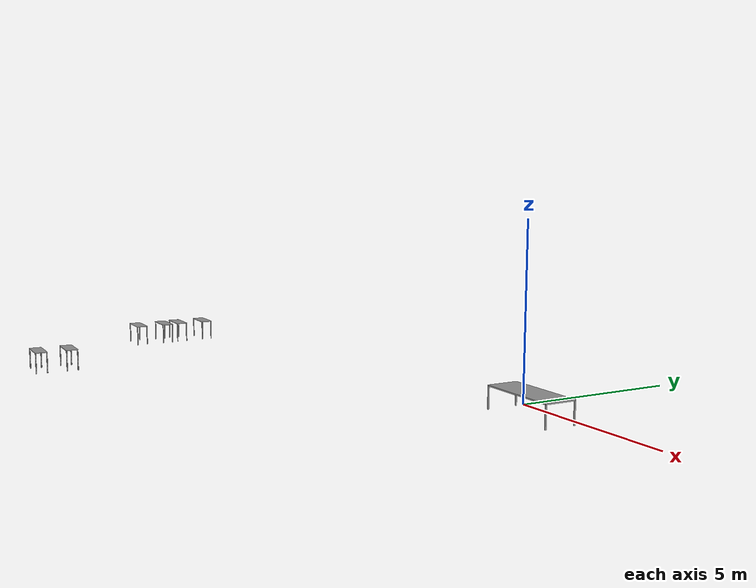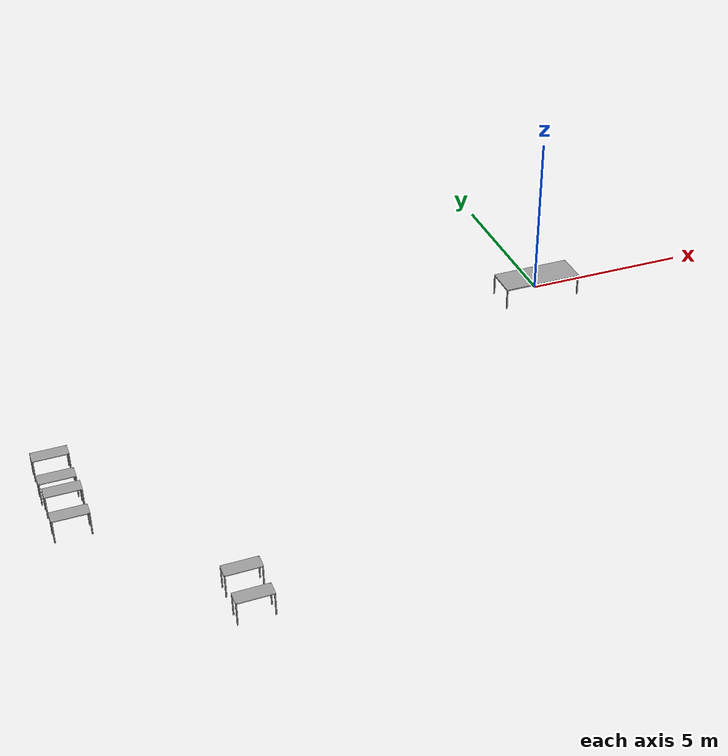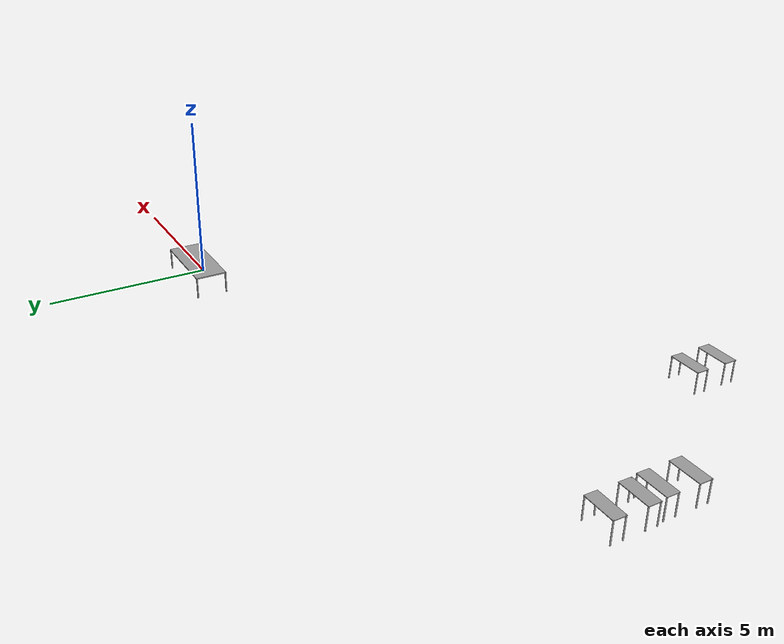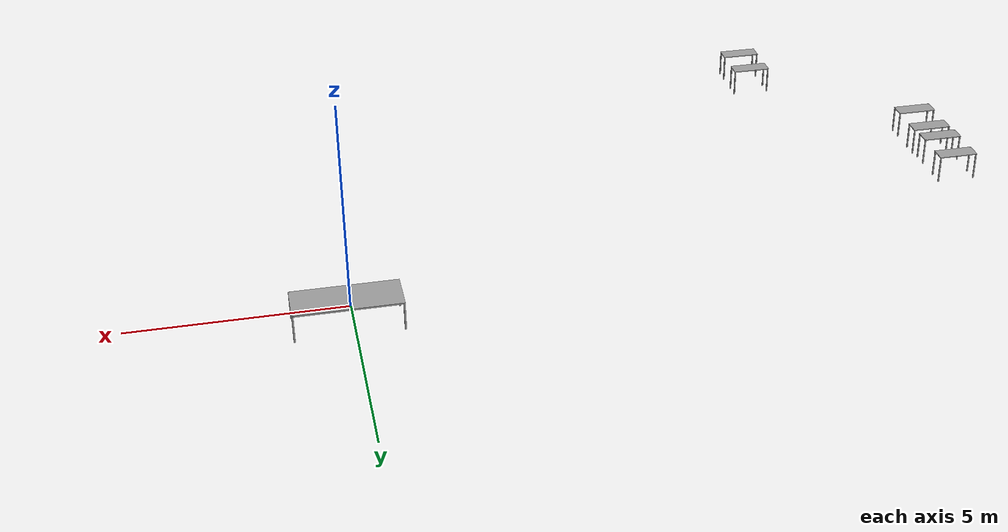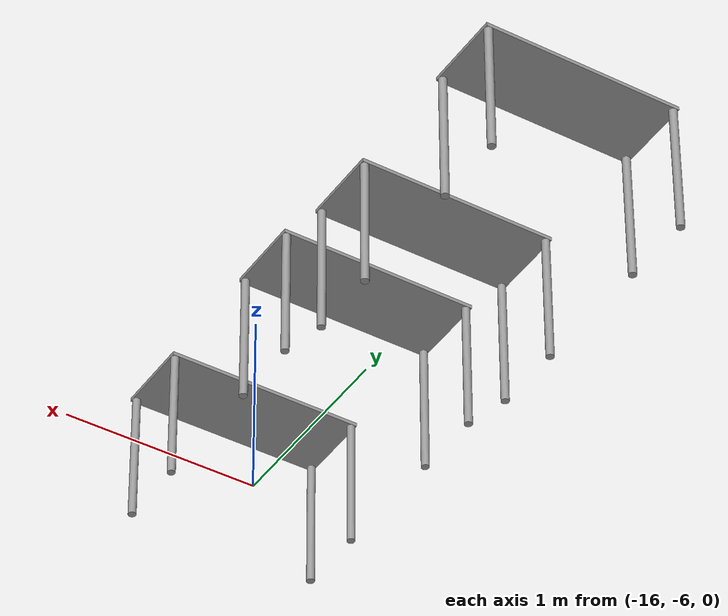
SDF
<?xml version='1.0'?>
<sdf version='1.6'>
  <model name='bigTable'>
    <link name='link_0'>
      <pose frame=''>0.097201 0.142857 0.331429 0 -0 0</pose>
      <inertial>
        <mass>1</mass>
        <inertia>
          <ixx>0.166667</ixx>
          <ixy>0</ixy>
          <ixz>0</ixz>
          <iyy>0.166667</iyy>
          <iyz>0</iyz>
          <izz>0.166667</izz>
        </inertia>
        <pose frame=''>0 0 0 0 -0 0</pose>
      </inertial>
      <gravity>1</gravity>
      <self_collide>0</self_collide>
      <kinematic>0</kinematic>
      <visual name='visual'>
        <pose frame=''>0 0 0 0 -0 0</pose>
        <geometry>
          <box>
            <size>2.5 1 0.04</size>
          </box>
        </geometry>
        <material>
          <lighting>1</lighting>
          <script>
            <uri>file://media/materials/scripts/gazebo.material</uri>
            <name>Gazebo/Grey</name>
          </script>
          <ambient>0.3 0.3 0.3 1</ambient>
          <diffuse>0.7 0.7 0.7 1</diffuse>
          <specular>0.01 0.01 0.01 1</specular>
          <emissive>0 0 0 1</emissive>
          <shader type='vertex'>
            <normal_map>__default__</normal_map>
          </shader>
        </material>
        <cast_shadows>1</cast_shadows>
        <transparency>0</transparency>
      </visual>
      <collision name='collision'>
        <laser_retro>0</laser_retro>
        <max_contacts>10</max_contacts>
        <pose frame=''>0 0 0 0 -0 0</pose>
        <geometry>
          <box>
            <size>2.5 1 0.04</size>
          </box>
        </geometry>
        <surface>
          <friction>
            <ode>
              <mu>1</mu>
              <mu2>1</mu2>
              <fdir1>0 0 0</fdir1>
              <slip1>0</slip1>
              <slip2>0</slip2>
            </ode>
            <torsional>
              <coefficient>1</coefficient>
              <patch_radius>0</patch_radius>
              <surface_radius>0</surface_radius>
              <use_patch_radius>1</use_patch_radius>
              <ode>
                <slip>0</slip>
              </ode>
            </torsional>
          </friction>
          <bounce>
            <restitution_coefficient>0</restitution_coefficient>
            <threshold>1e+06</threshold>
          </bounce>
          <contact>
            <collide_without_contact>0</collide_without_contact>
            <collide_without_contact_bitmask>1</collide_without_contact_bitmask>
            <collide_bitmask>1</collide_bitmask>
            <ode>
              <soft_cfm>0</soft_cfm>
              <soft_erp>0.2</soft_erp>
              <kp>1e+13</kp>
              <kd>1</kd>
              <max_vel>0.01</max_vel>
              <min_depth>0</min_depth>
            </ode>
            <bullet>
              <split_impulse>1</split_impulse>
              <split_impulse_penetration_threshold>-0.01</split_impulse_penetration_threshold>
              <soft_cfm>0</soft_cfm>
              <soft_erp>0.2</soft_erp>
              <kp>1e+13</kp>
              <kd>1</kd>
            </bullet>
          </contact>
        </surface>
      </collision>
    </link>
    <link name='link_1'>
      <pose frame=''>-1.1328 -0.337143 0.001429 0 -0 0</pose>
      <inertial>
        <mass>1</mass>
        <inertia>
          <ixx>0.166667</ixx>
          <ixy>0</ixy>
          <ixz>0</ixz>
          <iyy>0.166667</iyy>
          <iyz>0</iyz>
          <izz>0.166667</izz>
        </inertia>
        <pose frame=''>0 0 0 0 -0 0</pose>
      </inertial>
      <gravity>1</gravity>
      <self_collide>0</self_collide>
      <kinematic>0</kinematic>
      <visual name='visual'>
        <pose frame=''>0 0 0 0 -0 0</pose>
        <geometry>
          <box>
            <size>0.04 0.04 0.7</size>
          </box>
        </geometry>
        <material>
          <lighting>1</lighting>
          <script>
            <uri>file://media/materials/scripts/gazebo.material</uri>
            <name>Gazebo/Grey</name>
          </script>
          <ambient>0.3 0.3 0.3 1</ambient>
          <diffuse>0.7 0.7 0.7 1</diffuse>
          <specular>0.01 0.01 0.01 1</specular>
          <emissive>0 0 0 1</emissive>
          <shader type='vertex'>
            <normal_map>__default__</normal_map>
          </shader>
        </material>
        <cast_shadows>1</cast_shadows>
        <transparency>0</transparency>
      </visual>
      <collision name='collision'>
        <laser_retro>0</laser_retro>
        <max_contacts>10</max_contacts>
        <pose frame=''>0 0 0 0 -0 0</pose>
        <geometry>
          <box>
            <size>0.04 0.04 0.7</size>
          </box>
        </geometry>
        <surface>
          <friction>
            <ode>
              <mu>1</mu>
              <mu2>1</mu2>
              <fdir1>0 0 0</fdir1>
              <slip1>0</slip1>
              <slip2>0</slip2>
            </ode>
            <torsional>
              <coefficient>1</coefficient>
              <patch_radius>0</patch_radius>
              <surface_radius>0</surface_radius>
              <use_patch_radius>1</use_patch_radius>
              <ode>
                <slip>0</slip>
              </ode>
            </torsional>
          </friction>
          <bounce>
            <restitution_coefficient>0</restitution_coefficient>
            <threshold>1e+06</threshold>
          </bounce>
          <contact>
            <collide_without_contact>0</collide_without_contact>
            <collide_without_contact_bitmask>1</collide_without_contact_bitmask>
            <collide_bitmask>1</collide_bitmask>
            <ode>
              <soft_cfm>0</soft_cfm>
              <soft_erp>0.2</soft_erp>
              <kp>1e+13</kp>
              <kd>1</kd>
              <max_vel>0.01</max_vel>
              <min_depth>0</min_depth>
            </ode>
            <bullet>
              <split_impulse>1</split_impulse>
              <split_impulse_penetration_threshold>-0.01</split_impulse_penetration_threshold>
              <soft_cfm>0</soft_cfm>
              <soft_erp>0.2</soft_erp>
              <kp>1e+13</kp>
              <kd>1</kd>
            </bullet>
          </contact>
        </surface>
      </collision>
    </link>
    <link name='link_1_clone'>
      <pose frame=''>-1.1328 0.622857 0.001429 0 -0 0</pose>
      <inertial>
        <mass>1</mass>
        <inertia>
          <ixx>0.166667</ixx>
          <ixy>0</ixy>
          <ixz>0</ixz>
          <iyy>0.166667</iyy>
          <iyz>0</iyz>
          <izz>0.166667</izz>
        </inertia>
        <pose frame=''>0 0 0 0 -0 0</pose>
      </inertial>
      <self_collide>0</self_collide>
      <kinematic>0</kinematic>
      <visual name='visual'>
        <pose frame=''>0 0 0 0 -0 0</pose>
        <geometry>
          <box>
            <size>0.04 0.04 0.7</size>
          </box>
        </geometry>
        <material>
          <lighting>1</lighting>
          <script>
            <uri>file://media/materials/scripts/gazebo.material</uri>
            <name>Gazebo/Grey</name>
          </script>
          <ambient>0.3 0.3 0.3 1</ambient>
          <diffuse>0.7 0.7 0.7 1</diffuse>
          <specular>0.01 0.01 0.01 1</specular>
          <emissive>0 0 0 1</emissive>
          <shader type='vertex'>
            <normal_map>__default__</normal_map>
          </shader>
        </material>
        <cast_shadows>1</cast_shadows>
        <transparency>0</transparency>
      </visual>
      <collision name='collision'>
        <laser_retro>0</laser_retro>
        <max_contacts>10</max_contacts>
        <pose frame=''>0 0 0 0 -0 0</pose>
        <geometry>
          <box>
            <size>0.04 0.04 0.7</size>
          </box>
        </geometry>
        <surface>
          <friction>
            <ode>
              <mu>1</mu>
              <mu2>1</mu2>
              <fdir1>0 0 0</fdir1>
              <slip1>0</slip1>
              <slip2>0</slip2>
            </ode>
            <torsional>
              <coefficient>1</coefficient>
              <patch_radius>0</patch_radius>
              <surface_radius>0</surface_radius>
              <use_patch_radius>1</use_patch_radius>
              <ode>
                <slip>0</slip>
              </ode>
            </torsional>
          </friction>
          <bounce>
            <restitution_coefficient>0</restitution_coefficient>
            <threshold>1e+06</threshold>
          </bounce>
          <contact>
            <collide_without_contact>0</collide_without_contact>
            <collide_without_contact_bitmask>1</collide_without_contact_bitmask>
            <collide_bitmask>1</collide_bitmask>
            <ode>
              <soft_cfm>0</soft_cfm>
              <soft_erp>0.2</soft_erp>
              <kp>1e+13</kp>
              <kd>1</kd>
              <max_vel>0.01</max_vel>
              <min_depth>0</min_depth>
            </ode>
            <bullet>
              <split_impulse>1</split_impulse>
              <split_impulse_penetration_threshold>-0.01</split_impulse_penetration_threshold>
              <soft_cfm>0</soft_cfm>
              <soft_erp>0.2</soft_erp>
              <kp>1e+13</kp>
              <kd>1</kd>
            </bullet>
          </contact>
        </surface>
      </collision>
    </link>
    <link name='link_1_clone_0'>
      <pose frame=''>1.3272 0.622857 0.001429 0 -0 0</pose>
      <inertial>
        <mass>1</mass>
        <inertia>
          <ixx>0.166667</ixx>
          <ixy>0</ixy>
          <ixz>0</ixz>
          <iyy>0.166667</iyy>
          <iyz>0</iyz>
          <izz>0.166667</izz>
        </inertia>
        <pose frame=''>0 0 0 0 -0 0</pose>
      </inertial>
      <self_collide>0</self_collide>
      <kinematic>0</kinematic>
      <visual name='visual'>
        <pose frame=''>0 0 0 0 -0 0</pose>
        <geometry>
          <box>
            <size>0.04 0.04 0.7</size>
          </box>
        </geometry>
        <material>
          <lighting>1</lighting>
          <script>
            <uri>file://media/materials/scripts/gazebo.material</uri>
            <name>Gazebo/Grey</name>
          </script>
          <ambient>0.3 0.3 0.3 1</ambient>
          <diffuse>0.7 0.7 0.7 1</diffuse>
          <specular>0.01 0.01 0.01 1</specular>
          <emissive>0 0 0 1</emissive>
          <shader type='vertex'>
            <normal_map>__default__</normal_map>
          </shader>
        </material>
        <cast_shadows>1</cast_shadows>
        <transparency>0</transparency>
      </visual>
      <collision name='collision'>
        <laser_retro>0</laser_retro>
        <max_contacts>10</max_contacts>
        <pose frame=''>0 0 0 0 -0 0</pose>
        <geometry>
          <box>
            <size>0.04 0.04 0.7</size>
          </box>
        </geometry>
        <surface>
          <friction>
            <ode>
              <mu>1</mu>
              <mu2>1</mu2>
              <fdir1>0 0 0</fdir1>
              <slip1>0</slip1>
              <slip2>0</slip2>
            </ode>
            <torsional>
              <coefficient>1</coefficient>
              <patch_radius>0</patch_radius>
              <surface_radius>0</surface_radius>
              <use_patch_radius>1</use_patch_radius>
              <ode>
                <slip>0</slip>
              </ode>
            </torsional>
          </friction>
          <bounce>
            <restitution_coefficient>0</restitution_coefficient>
            <threshold>1e+06</threshold>
          </bounce>
          <contact>
            <collide_without_contact>0</collide_without_contact>
            <collide_without_contact_bitmask>1</collide_without_contact_bitmask>
            <collide_bitmask>1</collide_bitmask>
            <ode>
              <soft_cfm>0</soft_cfm>
              <soft_erp>0.2</soft_erp>
              <kp>1e+13</kp>
              <kd>1</kd>
              <max_vel>0.01</max_vel>
              <min_depth>0</min_depth>
            </ode>
            <bullet>
              <split_impulse>1</split_impulse>
              <split_impulse_penetration_threshold>-0.01</split_impulse_penetration_threshold>
              <soft_cfm>0</soft_cfm>
              <soft_erp>0.2</soft_erp>
              <kp>1e+13</kp>
              <kd>1</kd>
            </bullet>
          </contact>
        </surface>
      </collision>
    </link>
    <link name='link_1_clone_1'>
      <pose frame=''>1.3272 -0.337143 0.001429 0 -0 0</pose>
      <inertial>
        <mass>1</mass>
        <inertia>
          <ixx>0.166667</ixx>
          <ixy>0</ixy>
          <ixz>0</ixz>
          <iyy>0.166667</iyy>
          <iyz>0</iyz>
          <izz>0.166667</izz>
        </inertia>
        <pose frame=''>0 0 0 0 -0 0</pose>
      </inertial>
      <self_collide>0</self_collide>
      <kinematic>0</kinematic>
      <visual name='visual'>
        <pose frame=''>0 0 0 0 -0 0</pose>
        <geometry>
          <box>
            <size>0.04 0.04 0.7</size>
          </box>
        </geometry>
        <material>
          <lighting>1</lighting>
          <script>
            <uri>file://media/materials/scripts/gazebo.material</uri>
            <name>Gazebo/Grey</name>
          </script>
          <ambient>0.3 0.3 0.3 1</ambient>
          <diffuse>0.7 0.7 0.7 1</diffuse>
          <specular>0.01 0.01 0.01 1</specular>
          <emissive>0 0 0 1</emissive>
          <shader type='vertex'>
            <normal_map>__default__</normal_map>
          </shader>
        </material>
        <cast_shadows>1</cast_shadows>
        <transparency>0</transparency>
      </visual>
      <collision name='collision'>
        <laser_retro>0</laser_retro>
        <max_contacts>10</max_contacts>
        <pose frame=''>0 0 0 0 -0 0</pose>
        <geometry>
          <box>
            <size>0.04 0.04 0.7</size>
          </box>
        </geometry>
        <surface>
          <friction>
            <ode>
              <mu>1</mu>
              <mu2>1</mu2>
              <fdir1>0 0 0</fdir1>
              <slip1>0</slip1>
              <slip2>0</slip2>
            </ode>
            <torsional>
              <coefficient>1</coefficient>
              <patch_radius>0</patch_radius>
              <surface_radius>0</surface_radius>
              <use_patch_radius>1</use_patch_radius>
              <ode>
                <slip>0</slip>
              </ode>
            </torsional>
          </friction>
          <bounce>
            <restitution_coefficient>0</restitution_coefficient>
            <threshold>1e+06</threshold>
          </bounce>
          <contact>
            <collide_without_contact>0</collide_without_contact>
            <collide_without_contact_bitmask>1</collide_without_contact_bitmask>
            <collide_bitmask>1</collide_bitmask>
            <ode>
              <soft_cfm>0</soft_cfm>
              <soft_erp>0.2</soft_erp>
              <kp>1e+13</kp>
              <kd>1</kd>
              <max_vel>0.01</max_vel>
              <min_depth>0</min_depth>
            </ode>
            <bullet>
              <split_impulse>1</split_impulse>
              <split_impulse_penetration_threshold>-0.01</split_impulse_penetration_threshold>
              <soft_cfm>0</soft_cfm>
              <soft_erp>0.2</soft_erp>
              <kp>1e+13</kp>
              <kd>1</kd>
            </bullet>
          </contact>
        </surface>
      </collision>
    </link>
    <model name='Table'>
      <model name='Table'>
        <link name='link_1'>
          <pose frame=''>-0 0 0.272 0 -0 0</pose>
          <inertial>
            <mass>1</mass>
            <inertia>
              <ixx>0.166667</ixx>
              <ixy>0</ixy>
              <ixz>0</ixz>
              <iyy>0.166667</iyy>
              <iyz>0</iyz>
              <izz>0.166667</izz>
            </inertia>
            <pose frame=''>0 0 0 0 -0 0</pose>
          </inertial>
          <gravity>1</gravity>
          <self_collide>0</self_collide>
          <kinematic>0</kinematic>
          <visual name='visual'>
            <pose frame=''>0 0 0 0 -0 0</pose>
            <geometry>
              <box>
                <size>1 0.4 0.02</size>
              </box>
            </geometry>
            <material>
              <lighting>1</lighting>
              <script>
                <uri>file://media/materials/scripts/gazebo.material</uri>
                <name>Gazebo/Grey</name>
              </script>
              <ambient>0.3 0.3 0.3 1</ambient>
              <diffuse>0.7 0.7 0.7 1</diffuse>
              <specular>0.01 0.01 0.01 1</specular>
              <emissive>0 0 0 1</emissive>
              <shader type='vertex'>
                <normal_map>__default__</normal_map>
              </shader>
            </material>
            <cast_shadows>1</cast_shadows>
            <transparency>0</transparency>
          </visual>
          <collision name='collision'>
            <laser_retro>0</laser_retro>
            <max_contacts>10</max_contacts>
            <pose frame=''>0 0 0 0 -0 0</pose>
            <geometry>
              <box>
                <size>1 0.4 0.02</size>
              </box>
            </geometry>
            <surface>
              <friction>
                <ode>
                  <mu>1</mu>
                  <mu2>1</mu2>
                  <fdir1>0 0 0</fdir1>
                  <slip1>0</slip1>
                  <slip2>0</slip2>
                </ode>
                <torsional>
                  <coefficient>1</coefficient>
                  <patch_radius>0</patch_radius>
                  <surface_radius>0</surface_radius>
                  <use_patch_radius>1</use_patch_radius>
                  <ode>
                    <slip>0</slip>
                  </ode>
                </torsional>
              </friction>
              <bounce>
                <restitution_coefficient>0</restitution_coefficient>
                <threshold>1e+06</threshold>
              </bounce>
              <contact>
                <collide_without_contact>0</collide_without_contact>
                <collide_without_contact_bitmask>1</collide_without_contact_bitmask>
                <collide_bitmask>1</collide_bitmask>
                <ode>
                  <soft_cfm>0</soft_cfm>
                  <soft_erp>0.2</soft_erp>
                  <kp>1e+13</kp>
                  <kd>1</kd>
                  <max_vel>0.01</max_vel>
                  <min_depth>0</min_depth>
                </ode>
                <bullet>
                  <split_impulse>1</split_impulse>
                  <split_impulse_penetration_threshold>-0.01</split_impulse_penetration_threshold>
                  <soft_cfm>0</soft_cfm>
                  <soft_erp>0.2</soft_erp>
                  <kp>1e+13</kp>
                  <kd>1</kd>
                </bullet>
              </contact>
            </surface>
          </collision>
        </link>
        <link name='link_2_clone'>
          <pose frame=''>-0.48 0.18 -0.068 0 -0 0</pose>
          <inertial>
            <mass>1</mass>
            <inertia>
              <ixx>0.145833</ixx>
              <ixy>0</ixy>
              <ixz>0</ixz>
              <iyy>0.145833</iyy>
              <iyz>0</iyz>
              <izz>0.125</izz>
            </inertia>
            <pose frame=''>0 0 0 0 -0 0</pose>
          </inertial>
          <self_collide>0</self_collide>
          <kinematic>0</kinematic>
          <visual name='visual'>
            <pose frame=''>0 0 0 0 -0 0</pose>
            <geometry>
              <cylinder>
                <radius>0.02</radius>
                <length>0.7</length>
              </cylinder>
            </geometry>
            <material>
              <lighting>1</lighting>
              <script>
                <uri>file://media/materials/scripts/gazebo.material</uri>
                <name>Gazebo/Grey</name>
              </script>
              <ambient>0.3 0.3 0.3 1</ambient>
              <diffuse>0.7 0.7 0.7 1</diffuse>
              <specular>0.01 0.01 0.01 1</specular>
              <emissive>0 0 0 1</emissive>
              <shader type='vertex'>
                <normal_map>__default__</normal_map>
              </shader>
            </material>
            <cast_shadows>1</cast_shadows>
            <transparency>0</transparency>
          </visual>
          <collision name='collision'>
            <laser_retro>0</laser_retro>
            <max_contacts>10</max_contacts>
            <pose frame=''>0 0 0 0 -0 0</pose>
            <geometry>
              <cylinder>
                <radius>0.02</radius>
                <length>0.7</length>
              </cylinder>
            </geometry>
            <surface>
              <friction>
                <ode>
                  <mu>1</mu>
                  <mu2>1</mu2>
                  <fdir1>0 0 0</fdir1>
                  <slip1>0</slip1>
                  <slip2>0</slip2>
                </ode>
                <torsional>
                  <coefficient>1</coefficient>
                  <patch_radius>0</patch_radius>
                  <surface_radius>0</surface_radius>
                  <use_patch_radius>1</use_patch_radius>
                  <ode>
                    <slip>0</slip>
                  </ode>
                </torsional>
              </friction>
              <bounce>
                <restitution_coefficient>0</restitution_coefficient>
                <threshold>1e+06</threshold>
              </bounce>
              <contact>
                <collide_without_contact>0</collide_without_contact>
                <collide_without_contact_bitmask>1</collide_without_contact_bitmask>
                <collide_bitmask>1</collide_bitmask>
                <ode>
                  <soft_cfm>0</soft_cfm>
                  <soft_erp>0.2</soft_erp>
                  <kp>1e+13</kp>
                  <kd>1</kd>
                  <max_vel>0.01</max_vel>
                  <min_depth>0</min_depth>
                </ode>
                <bullet>
                  <split_impulse>1</split_impulse>
                  <split_impulse_penetration_threshold>-0.01</split_impulse_penetration_threshold>
                  <soft_cfm>0</soft_cfm>
                  <soft_erp>0.2</soft_erp>
                  <kp>1e+13</kp>
                  <kd>1</kd>
                </bullet>
              </contact>
            </surface>
          </collision>
        </link>
        <link name='link_2_clone_0'>
          <pose frame=''>0.479999 -0.18 -0.068 0 -0 0</pose>
          <inertial>
            <mass>1</mass>
            <inertia>
              <ixx>0.145833</ixx>
              <ixy>0</ixy>
              <ixz>0</ixz>
              <iyy>0.145833</iyy>
              <iyz>0</iyz>
              <izz>0.125</izz>
            </inertia>
            <pose frame=''>0 0 0 0 -0 0</pose>
          </inertial>
          <self_collide>0</self_collide>
          <kinematic>0</kinematic>
          <visual name='visual'>
            <pose frame=''>0 0 0 0 -0 0</pose>
            <geometry>
              <cylinder>
                <radius>0.02</radius>
                <length>0.7</length>
              </cylinder>
            </geometry>
            <material>
              <lighting>1</lighting>
              <script>
                <uri>file://media/materials/scripts/gazebo.material</uri>
                <name>Gazebo/Grey</name>
              </script>
              <ambient>0.3 0.3 0.3 1</ambient>
              <diffuse>0.7 0.7 0.7 1</diffuse>
              <specular>0.01 0.01 0.01 1</specular>
              <emissive>0 0 0 1</emissive>
              <shader type='vertex'>
                <normal_map>__default__</normal_map>
              </shader>
            </material>
            <cast_shadows>1</cast_shadows>
            <transparency>0</transparency>
          </visual>
          <collision name='collision'>
            <laser_retro>0</laser_retro>
            <max_contacts>10</max_contacts>
            <pose frame=''>0 0 0 0 -0 0</pose>
            <geometry>
              <cylinder>
                <radius>0.02</radius>
                <length>0.7</length>
              </cylinder>
            </geometry>
            <surface>
              <friction>
                <ode>
                  <mu>1</mu>
                  <mu2>1</mu2>
                  <fdir1>0 0 0</fdir1>
                  <slip1>0</slip1>
                  <slip2>0</slip2>
                </ode>
                <torsional>
                  <coefficient>1</coefficient>
                  <patch_radius>0</patch_radius>
                  <surface_radius>0</surface_radius>
                  <use_patch_radius>1</use_patch_radius>
                  <ode>
                    <slip>0</slip>
                  </ode>
                </torsional>
              </friction>
              <bounce>
                <restitution_coefficient>0</restitution_coefficient>
                <threshold>1e+06</threshold>
              </bounce>
              <contact>
                <collide_without_contact>0</collide_without_contact>
                <collide_without_contact_bitmask>1</collide_without_contact_bitmask>
                <collide_bitmask>1</collide_bitmask>
                <ode>
                  <soft_cfm>0</soft_cfm>
                  <soft_erp>0.2</soft_erp>
                  <kp>1e+13</kp>
                  <kd>1</kd>
                  <max_vel>0.01</max_vel>
                  <min_depth>0</min_depth>
                </ode>
                <bullet>
                  <split_impulse>1</split_impulse>
                  <split_impulse_penetration_threshold>-0.01</split_impulse_penetration_threshold>
                  <soft_cfm>0</soft_cfm>
                  <soft_erp>0.2</soft_erp>
                  <kp>1e+13</kp>
                  <kd>1</kd>
                </bullet>
              </contact>
            </surface>
          </collision>
        </link>
        <link name='link_2_clone_0_clone'>
          <pose frame=''>-0.48 -0.18 -0.068 0 -0 0</pose>
          <inertial>
            <mass>1</mass>
            <inertia>
              <ixx>0.145833</ixx>
              <ixy>0</ixy>
              <ixz>0</ixz>
              <iyy>0.145833</iyy>
              <iyz>0</iyz>
              <izz>0.125</izz>
            </inertia>
            <pose frame=''>0 0 0 0 -0 0</pose>
          </inertial>
          <self_collide>0</self_collide>
          <kinematic>0</kinematic>
          <visual name='visual'>
            <pose frame=''>0 0 0 0 -0 0</pose>
            <geometry>
              <cylinder>
                <radius>0.02</radius>
                <length>0.7</length>
              </cylinder>
            </geometry>
            <material>
              <lighting>1</lighting>
              <script>
                <uri>file://media/materials/scripts/gazebo.material</uri>
                <name>Gazebo/Grey</name>
              </script>
              <ambient>0.3 0.3 0.3 1</ambient>
              <diffuse>0.7 0.7 0.7 1</diffuse>
              <specular>0.01 0.01 0.01 1</specular>
              <emissive>0 0 0 1</emissive>
              <shader type='vertex'>
                <normal_map>__default__</normal_map>
              </shader>
            </material>
            <cast_shadows>1</cast_shadows>
            <transparency>0</transparency>
          </visual>
          <collision name='collision'>
            <laser_retro>0</laser_retro>
            <max_contacts>10</max_contacts>
            <pose frame=''>0 0 0 0 -0 0</pose>
            <geometry>
              <cylinder>
                <radius>0.02</radius>
                <length>0.7</length>
              </cylinder>
            </geometry>
            <surface>
              <friction>
                <ode>
                  <mu>1</mu>
                  <mu2>1</mu2>
                  <fdir1>0 0 0</fdir1>
                  <slip1>0</slip1>
                  <slip2>0</slip2>
                </ode>
                <torsional>
                  <coefficient>1</coefficient>
                  <patch_radius>0</patch_radius>
                  <surface_radius>0</surface_radius>
                  <use_patch_radius>1</use_patch_radius>
                  <ode>
                    <slip>0</slip>
                  </ode>
                </torsional>
              </friction>
              <bounce>
                <restitution_coefficient>0</restitution_coefficient>
                <threshold>1e+06</threshold>
              </bounce>
              <contact>
                <collide_without_contact>0</collide_without_contact>
                <collide_without_contact_bitmask>1</collide_without_contact_bitmask>
                <collide_bitmask>1</collide_bitmask>
                <ode>
                  <soft_cfm>0</soft_cfm>
                  <soft_erp>0.2</soft_erp>
                  <kp>1e+13</kp>
                  <kd>1</kd>
                  <max_vel>0.01</max_vel>
                  <min_depth>0</min_depth>
                </ode>
                <bullet>
                  <split_impulse>1</split_impulse>
                  <split_impulse_penetration_threshold>-0.01</split_impulse_penetration_threshold>
                  <soft_cfm>0</soft_cfm>
                  <soft_erp>0.2</soft_erp>
                  <kp>1e+13</kp>
                  <kd>1</kd>
                </bullet>
              </contact>
            </surface>
          </collision>
        </link>
        <link name='link_2_clone_1'>
          <pose frame=''>0.479999 0.18 -0.068 0 -0 0</pose>
          <inertial>
            <mass>1</mass>
            <inertia>
              <ixx>0.145833</ixx>
              <ixy>0</ixy>
              <ixz>0</ixz>
              <iyy>0.145833</iyy>
              <iyz>0</iyz>
              <izz>0.125</izz>
            </inertia>
            <pose frame=''>0 0 0 0 -0 0</pose>
          </inertial>
          <self_collide>0</self_collide>
          <kinematic>0</kinematic>
          <visual name='visual'>
            <pose frame=''>0 0 0 0 -0 0</pose>
            <geometry>
              <cylinder>
                <radius>0.02</radius>
                <length>0.7</length>
              </cylinder>
            </geometry>
            <material>
              <lighting>1</lighting>
              <script>
                <uri>file://media/materials/scripts/gazebo.material</uri>
                <name>Gazebo/Grey</name>
              </script>
              <ambient>0.3 0.3 0.3 1</ambient>
              <diffuse>0.7 0.7 0.7 1</diffuse>
              <specular>0.01 0.01 0.01 1</specular>
              <emissive>0 0 0 1</emissive>
              <shader type='vertex'>
                <normal_map>__default__</normal_map>
              </shader>
            </material>
            <cast_shadows>1</cast_shadows>
            <transparency>0</transparency>
          </visual>
          <collision name='collision'>
            <laser_retro>0</laser_retro>
            <max_contacts>10</max_contacts>
            <pose frame=''>0 0 0 0 -0 0</pose>
            <geometry>
              <cylinder>
                <radius>0.02</radius>
                <length>0.7</length>
              </cylinder>
            </geometry>
            <surface>
              <friction>
                <ode>
                  <mu>1</mu>
                  <mu2>1</mu2>
                  <fdir1>0 0 0</fdir1>
                  <slip1>0</slip1>
                  <slip2>0</slip2>
                </ode>
                <torsional>
                  <coefficient>1</coefficient>
                  <patch_radius>0</patch_radius>
                  <surface_radius>0</surface_radius>
                  <use_patch_radius>1</use_patch_radius>
                  <ode>
                    <slip>0</slip>
                  </ode>
                </torsional>
              </friction>
              <bounce>
                <restitution_coefficient>0</restitution_coefficient>
                <threshold>1e+06</threshold>
              </bounce>
              <contact>
                <collide_without_contact>0</collide_without_contact>
                <collide_without_contact_bitmask>1</collide_without_contact_bitmask>
                <collide_bitmask>1</collide_bitmask>
                <ode>
                  <soft_cfm>0</soft_cfm>
                  <soft_erp>0.2</soft_erp>
                  <kp>1e+13</kp>
                  <kd>1</kd>
                  <max_vel>0.01</max_vel>
                  <min_depth>0</min_depth>
                </ode>
                <bullet>
                  <split_impulse>1</split_impulse>
                  <split_impulse_penetration_threshold>-0.01</split_impulse_penetration_threshold>
                  <soft_cfm>0</soft_cfm>
                  <soft_erp>0.2</soft_erp>
                  <kp>1e+13</kp>
                  <kd>1</kd>
                </bullet>
              </contact>
            </surface>
          </collision>
        </link>
        <joint name='link_1_JOINT_1' type='revolute'>
          <parent>link_1</parent>
          <child>link_2_clone</child>
          <pose frame=''>0 0 0 0 -0 0</pose>
          <axis>
            <xyz>1 0 0</xyz>
            <use_parent_model_frame>0</use_parent_model_frame>
            <limit>
              <lower>-1.79769e+308</lower>
              <upper>1.79769e+308</upper>
              <effort>-1</effort>
              <velocity>-1</velocity>
            </limit>
            <dynamics>
              <spring_reference>0</spring_reference>
              <spring_stiffness>0</spring_stiffness>
              <damping>0</damping>
            </dynamics>
          </axis>
          <physics>
            <ode>
              <limit>
                <cfm>0</cfm>
                <erp>0.2</erp>
              </limit>
              <suspension>
                <cfm>0</cfm>
                <erp>0.2</erp>
              </suspension>
            </ode>
          </physics>
        </joint>
        <joint name='link_1_JOINT_2' type='revolute'>
          <parent>link_1</parent>
          <child>link_2_clone_1</child>
          <pose frame=''>0 0 0 0 -0 0</pose>
          <axis>
            <xyz>1 0 0</xyz>
            <use_parent_model_frame>0</use_parent_model_frame>
            <limit>
              <lower>-1.79769e+308</lower>
              <upper>1.79769e+308</upper>
              <effort>-1</effort>
              <velocity>-1</velocity>
            </limit>
            <dynamics>
              <spring_reference>0</spring_reference>
              <spring_stiffness>0</spring_stiffness>
              <damping>0</damping>
            </dynamics>
          </axis>
          <physics>
            <ode>
              <limit>
                <cfm>0</cfm>
                <erp>0.2</erp>
              </limit>
              <suspension>
                <cfm>0</cfm>
                <erp>0.2</erp>
              </suspension>
            </ode>
          </physics>
        </joint>
        <joint name='link_1_JOINT_3' type='revolute'>
          <parent>link_1</parent>
          <child>link_2_clone_0</child>
          <pose frame=''>0 0 0 0 -0 0</pose>
          <axis>
            <xyz>1 0 0</xyz>
            <use_parent_model_frame>0</use_parent_model_frame>
            <limit>
              <lower>-1.79769e+308</lower>
              <upper>1.79769e+308</upper>
              <effort>-1</effort>
              <velocity>-1</velocity>
            </limit>
            <dynamics>
              <spring_reference>0</spring_reference>
              <spring_stiffness>0</spring_stiffness>
              <damping>0</damping>
            </dynamics>
          </axis>
          <physics>
            <ode>
              <limit>
                <cfm>0</cfm>
                <erp>0.2</erp>
              </limit>
              <suspension>
                <cfm>0</cfm>
                <erp>0.2</erp>
              </suspension>
            </ode>
          </physics>
        </joint>
        <joint name='link_1_JOINT_4' type='revolute'>
          <parent>link_1</parent>
          <child>link_2_clone_0_clone</child>
          <pose frame=''>0 0 0 0 -0 0</pose>
          <axis>
            <xyz>1 0 0</xyz>
            <use_parent_model_frame>0</use_parent_model_frame>
            <limit>
              <lower>-1.79769e+308</lower>
              <upper>1.79769e+308</upper>
              <effort>-1</effort>
              <velocity>-1</velocity>
            </limit>
            <dynamics>
              <spring_reference>0</spring_reference>
              <spring_stiffness>0</spring_stiffness>
              <damping>0</damping>
            </dynamics>
          </axis>
          <physics>
            <ode>
              <limit>
                <cfm>0</cfm>
                <erp>0.2</erp>
              </limit>
              <suspension>
                <cfm>0</cfm>
                <erp>0.2</erp>
              </suspension>
            </ode>
          </physics>
        </joint>
        <static>0</static>
        <allow_auto_disable>1</allow_auto_disable>
        <pose frame=''>-15.6938 -3.46397 0.228 0 -0 0</pose>
      </model>
      <model name='Table_0'>
        <link name='link_1'>
          <pose frame=''>-0 0 0.272 0 -0 0</pose>
          <inertial>
            <mass>1</mass>
            <inertia>
              <ixx>0.166667</ixx>
              <ixy>0</ixy>
              <ixz>0</ixz>
              <iyy>0.166667</iyy>
              <iyz>0</iyz>
              <izz>0.166667</izz>
            </inertia>
            <pose frame=''>0 0 0 0 -0 0</pose>
          </inertial>
          <gravity>1</gravity>
          <self_collide>0</self_collide>
          <kinematic>0</kinematic>
          <visual name='visual'>
            <pose frame=''>0 0 0 0 -0 0</pose>
            <geometry>
              <box>
                <size>1 0.4 0.02</size>
              </box>
            </geometry>
            <material>
              <lighting>1</lighting>
              <script>
                <uri>file://media/materials/scripts/gazebo.material</uri>
                <name>Gazebo/Grey</name>
              </script>
              <ambient>0.3 0.3 0.3 1</ambient>
              <diffuse>0.7 0.7 0.7 1</diffuse>
              <specular>0.01 0.01 0.01 1</specular>
              <emissive>0 0 0 1</emissive>
              <shader type='vertex'>
                <normal_map>__default__</normal_map>
              </shader>
            </material>
            <cast_shadows>1</cast_shadows>
            <transparency>0</transparency>
          </visual>
          <collision name='collision'>
            <laser_retro>0</laser_retro>
            <max_contacts>10</max_contacts>
            <pose frame=''>0 0 0 0 -0 0</pose>
            <geometry>
              <box>
                <size>1 0.4 0.02</size>
              </box>
            </geometry>
            <surface>
              <friction>
                <ode>
                  <mu>1</mu>
                  <mu2>1</mu2>
                  <fdir1>0 0 0</fdir1>
                  <slip1>0</slip1>
                  <slip2>0</slip2>
                </ode>
                <torsional>
                  <coefficient>1</coefficient>
                  <patch_radius>0</patch_radius>
                  <surface_radius>0</surface_radius>
                  <use_patch_radius>1</use_patch_radius>
                  <ode>
                    <slip>0</slip>
                  </ode>
                </torsional>
              </friction>
              <bounce>
                <restitution_coefficient>0</restitution_coefficient>
                <threshold>1e+06</threshold>
              </bounce>
              <contact>
                <collide_without_contact>0</collide_without_contact>
                <collide_without_contact_bitmask>1</collide_without_contact_bitmask>
                <collide_bitmask>1</collide_bitmask>
                <ode>
                  <soft_cfm>0</soft_cfm>
                  <soft_erp>0.2</soft_erp>
                  <kp>1e+13</kp>
                  <kd>1</kd>
                  <max_vel>0.01</max_vel>
                  <min_depth>0</min_depth>
                </ode>
                <bullet>
                  <split_impulse>1</split_impulse>
                  <split_impulse_penetration_threshold>-0.01</split_impulse_penetration_threshold>
                  <soft_cfm>0</soft_cfm>
                  <soft_erp>0.2</soft_erp>
                  <kp>1e+13</kp>
                  <kd>1</kd>
                </bullet>
              </contact>
            </surface>
          </collision>
        </link>
        <link name='link_2_clone'>
          <pose frame=''>-0.48 0.18 -0.068 0 -0 0</pose>
          <inertial>
            <mass>1</mass>
            <inertia>
              <ixx>0.145833</ixx>
              <ixy>0</ixy>
              <ixz>0</ixz>
              <iyy>0.145833</iyy>
              <iyz>0</iyz>
              <izz>0.125</izz>
            </inertia>
            <pose frame=''>0 0 0 0 -0 0</pose>
          </inertial>
          <self_collide>0</self_collide>
          <kinematic>0</kinematic>
          <visual name='visual'>
            <pose frame=''>0 0 0 0 -0 0</pose>
            <geometry>
              <cylinder>
                <radius>0.02</radius>
                <length>0.7</length>
              </cylinder>
            </geometry>
            <material>
              <lighting>1</lighting>
              <script>
                <uri>file://media/materials/scripts/gazebo.material</uri>
                <name>Gazebo/Grey</name>
              </script>
              <ambient>0.3 0.3 0.3 1</ambient>
              <diffuse>0.7 0.7 0.7 1</diffuse>
              <specular>0.01 0.01 0.01 1</specular>
              <emissive>0 0 0 1</emissive>
              <shader type='vertex'>
                <normal_map>__default__</normal_map>
              </shader>
            </material>
            <cast_shadows>1</cast_shadows>
            <transparency>0</transparency>
          </visual>
          <collision name='collision'>
            <laser_retro>0</laser_retro>
            <max_contacts>10</max_contacts>
            <pose frame=''>0 0 0 0 -0 0</pose>
            <geometry>
              <cylinder>
                <radius>0.02</radius>
                <length>0.7</length>
              </cylinder>
            </geometry>
            <surface>
              <friction>
                <ode>
                  <mu>1</mu>
                  <mu2>1</mu2>
                  <fdir1>0 0 0</fdir1>
                  <slip1>0</slip1>
                  <slip2>0</slip2>
                </ode>
                <torsional>
                  <coefficient>1</coefficient>
                  <patch_radius>0</patch_radius>
                  <surface_radius>0</surface_radius>
                  <use_patch_radius>1</use_patch_radius>
                  <ode>
                    <slip>0</slip>
                  </ode>
                </torsional>
              </friction>
              <bounce>
                <restitution_coefficient>0</restitution_coefficient>
                <threshold>1e+06</threshold>
              </bounce>
              <contact>
                <collide_without_contact>0</collide_without_contact>
                <collide_without_contact_bitmask>1</collide_without_contact_bitmask>
                <collide_bitmask>1</collide_bitmask>
                <ode>
                  <soft_cfm>0</soft_cfm>
                  <soft_erp>0.2</soft_erp>
                  <kp>1e+13</kp>
                  <kd>1</kd>
                  <max_vel>0.01</max_vel>
                  <min_depth>0</min_depth>
                </ode>
                <bullet>
                  <split_impulse>1</split_impulse>
                  <split_impulse_penetration_threshold>-0.01</split_impulse_penetration_threshold>
                  <soft_cfm>0</soft_cfm>
                  <soft_erp>0.2</soft_erp>
                  <kp>1e+13</kp>
                  <kd>1</kd>
                </bullet>
              </contact>
            </surface>
          </collision>
        </link>
        <link name='link_2_clone_0'>
          <pose frame=''>0.479999 -0.18 -0.068 0 -0 0</pose>
          <inertial>
            <mass>1</mass>
            <inertia>
              <ixx>0.145833</ixx>
              <ixy>0</ixy>
              <ixz>0</ixz>
              <iyy>0.145833</iyy>
              <iyz>0</iyz>
              <izz>0.125</izz>
            </inertia>
            <pose frame=''>0 0 0 0 -0 0</pose>
          </inertial>
          <self_collide>0</self_collide>
          <kinematic>0</kinematic>
          <visual name='visual'>
            <pose frame=''>0 0 0 0 -0 0</pose>
            <geometry>
              <cylinder>
                <radius>0.02</radius>
                <length>0.7</length>
              </cylinder>
            </geometry>
            <material>
              <lighting>1</lighting>
              <script>
                <uri>file://media/materials/scripts/gazebo.material</uri>
                <name>Gazebo/Grey</name>
              </script>
              <ambient>0.3 0.3 0.3 1</ambient>
              <diffuse>0.7 0.7 0.7 1</diffuse>
              <specular>0.01 0.01 0.01 1</specular>
              <emissive>0 0 0 1</emissive>
              <shader type='vertex'>
                <normal_map>__default__</normal_map>
              </shader>
            </material>
            <cast_shadows>1</cast_shadows>
            <transparency>0</transparency>
          </visual>
          <collision name='collision'>
            <laser_retro>0</laser_retro>
            <max_contacts>10</max_contacts>
            <pose frame=''>0 0 0 0 -0 0</pose>
            <geometry>
              <cylinder>
                <radius>0.02</radius>
                <length>0.7</length>
              </cylinder>
            </geometry>
            <surface>
              <friction>
                <ode>
                  <mu>1</mu>
                  <mu2>1</mu2>
                  <fdir1>0 0 0</fdir1>
                  <slip1>0</slip1>
                  <slip2>0</slip2>
                </ode>
                <torsional>
                  <coefficient>1</coefficient>
                  <patch_radius>0</patch_radius>
                  <surface_radius>0</surface_radius>
                  <use_patch_radius>1</use_patch_radius>
                  <ode>
                    <slip>0</slip>
                  </ode>
                </torsional>
              </friction>
              <bounce>
                <restitution_coefficient>0</restitution_coefficient>
                <threshold>1e+06</threshold>
              </bounce>
              <contact>
                <collide_without_contact>0</collide_without_contact>
                <collide_without_contact_bitmask>1</collide_without_contact_bitmask>
                <collide_bitmask>1</collide_bitmask>
                <ode>
                  <soft_cfm>0</soft_cfm>
                  <soft_erp>0.2</soft_erp>
                  <kp>1e+13</kp>
                  <kd>1</kd>
                  <max_vel>0.01</max_vel>
                  <min_depth>0</min_depth>
                </ode>
                <bullet>
                  <split_impulse>1</split_impulse>
                  <split_impulse_penetration_threshold>-0.01</split_impulse_penetration_threshold>
                  <soft_cfm>0</soft_cfm>
                  <soft_erp>0.2</soft_erp>
                  <kp>1e+13</kp>
                  <kd>1</kd>
                </bullet>
              </contact>
            </surface>
          </collision>
        </link>
        <link name='link_2_clone_0_clone'>
          <pose frame=''>-0.48 -0.18 -0.068 0 -0 0</pose>
          <inertial>
            <mass>1</mass>
            <inertia>
              <ixx>0.145833</ixx>
              <ixy>0</ixy>
              <ixz>0</ixz>
              <iyy>0.145833</iyy>
              <iyz>0</iyz>
              <izz>0.125</izz>
            </inertia>
            <pose frame=''>0 0 0 0 -0 0</pose>
          </inertial>
          <self_collide>0</self_collide>
          <kinematic>0</kinematic>
          <visual name='visual'>
            <pose frame=''>0 0 0 0 -0 0</pose>
            <geometry>
              <cylinder>
                <radius>0.02</radius>
                <length>0.7</length>
              </cylinder>
            </geometry>
            <material>
              <lighting>1</lighting>
              <script>
                <uri>file://media/materials/scripts/gazebo.material</uri>
                <name>Gazebo/Grey</name>
              </script>
              <ambient>0.3 0.3 0.3 1</ambient>
              <diffuse>0.7 0.7 0.7 1</diffuse>
              <specular>0.01 0.01 0.01 1</specular>
              <emissive>0 0 0 1</emissive>
              <shader type='vertex'>
                <normal_map>__default__</normal_map>
              </shader>
            </material>
            <cast_shadows>1</cast_shadows>
            <transparency>0</transparency>
          </visual>
          <collision name='collision'>
            <laser_retro>0</laser_retro>
            <max_contacts>10</max_contacts>
            <pose frame=''>0 0 0 0 -0 0</pose>
            <geometry>
              <cylinder>
                <radius>0.02</radius>
                <length>0.7</length>
              </cylinder>
            </geometry>
            <surface>
              <friction>
                <ode>
                  <mu>1</mu>
                  <mu2>1</mu2>
                  <fdir1>0 0 0</fdir1>
                  <slip1>0</slip1>
                  <slip2>0</slip2>
                </ode>
                <torsional>
                  <coefficient>1</coefficient>
                  <patch_radius>0</patch_radius>
                  <surface_radius>0</surface_radius>
                  <use_patch_radius>1</use_patch_radius>
                  <ode>
                    <slip>0</slip>
                  </ode>
                </torsional>
              </friction>
              <bounce>
                <restitution_coefficient>0</restitution_coefficient>
                <threshold>1e+06</threshold>
              </bounce>
              <contact>
                <collide_without_contact>0</collide_without_contact>
                <collide_without_contact_bitmask>1</collide_without_contact_bitmask>
                <collide_bitmask>1</collide_bitmask>
                <ode>
                  <soft_cfm>0</soft_cfm>
                  <soft_erp>0.2</soft_erp>
                  <kp>1e+13</kp>
                  <kd>1</kd>
                  <max_vel>0.01</max_vel>
                  <min_depth>0</min_depth>
                </ode>
                <bullet>
                  <split_impulse>1</split_impulse>
                  <split_impulse_penetration_threshold>-0.01</split_impulse_penetration_threshold>
                  <soft_cfm>0</soft_cfm>
                  <soft_erp>0.2</soft_erp>
                  <kp>1e+13</kp>
                  <kd>1</kd>
                </bullet>
              </contact>
            </surface>
          </collision>
        </link>
        <link name='link_2_clone_1'>
          <pose frame=''>0.479999 0.18 -0.068 0 -0 0</pose>
          <inertial>
            <mass>1</mass>
            <inertia>
              <ixx>0.145833</ixx>
              <ixy>0</ixy>
              <ixz>0</ixz>
              <iyy>0.145833</iyy>
              <iyz>0</iyz>
              <izz>0.125</izz>
            </inertia>
            <pose frame=''>0 0 0 0 -0 0</pose>
          </inertial>
          <self_collide>0</self_collide>
          <kinematic>0</kinematic>
          <visual name='visual'>
            <pose frame=''>0 0 0 0 -0 0</pose>
            <geometry>
              <cylinder>
                <radius>0.02</radius>
                <length>0.7</length>
              </cylinder>
            </geometry>
            <material>
              <lighting>1</lighting>
              <script>
                <uri>file://media/materials/scripts/gazebo.material</uri>
                <name>Gazebo/Grey</name>
              </script>
              <ambient>0.3 0.3 0.3 1</ambient>
              <diffuse>0.7 0.7 0.7 1</diffuse>
              <specular>0.01 0.01 0.01 1</specular>
              <emissive>0 0 0 1</emissive>
              <shader type='vertex'>
                <normal_map>__default__</normal_map>
              </shader>
            </material>
            <cast_shadows>1</cast_shadows>
            <transparency>0</transparency>
          </visual>
          <collision name='collision'>
            <laser_retro>0</laser_retro>
            <max_contacts>10</max_contacts>
            <pose frame=''>0 0 0 0 -0 0</pose>
            <geometry>
              <cylinder>
                <radius>0.02</radius>
                <length>0.7</length>
              </cylinder>
            </geometry>
            <surface>
              <friction>
                <ode>
                  <mu>1</mu>
                  <mu2>1</mu2>
                  <fdir1>0 0 0</fdir1>
                  <slip1>0</slip1>
                  <slip2>0</slip2>
                </ode>
                <torsional>
                  <coefficient>1</coefficient>
                  <patch_radius>0</patch_radius>
                  <surface_radius>0</surface_radius>
                  <use_patch_radius>1</use_patch_radius>
                  <ode>
                    <slip>0</slip>
                  </ode>
                </torsional>
              </friction>
              <bounce>
                <restitution_coefficient>0</restitution_coefficient>
                <threshold>1e+06</threshold>
              </bounce>
              <contact>
                <collide_without_contact>0</collide_without_contact>
                <collide_without_contact_bitmask>1</collide_without_contact_bitmask>
                <collide_bitmask>1</collide_bitmask>
                <ode>
                  <soft_cfm>0</soft_cfm>
                  <soft_erp>0.2</soft_erp>
                  <kp>1e+13</kp>
                  <kd>1</kd>
                  <max_vel>0.01</max_vel>
                  <min_depth>0</min_depth>
                </ode>
                <bullet>
                  <split_impulse>1</split_impulse>
                  <split_impulse_penetration_threshold>-0.01</split_impulse_penetration_threshold>
                  <soft_cfm>0</soft_cfm>
                  <soft_erp>0.2</soft_erp>
                  <kp>1e+13</kp>
                  <kd>1</kd>
                </bullet>
              </contact>
            </surface>
          </collision>
        </link>
        <joint name='link_1_JOINT_1' type='revolute'>
          <parent>link_1</parent>
          <child>link_2_clone</child>
          <pose frame=''>0 0 0 0 -0 0</pose>
          <axis>
            <xyz>1 0 0</xyz>
            <use_parent_model_frame>0</use_parent_model_frame>
            <limit>
              <lower>-1.79769e+308</lower>
              <upper>1.79769e+308</upper>
              <effort>-1</effort>
              <velocity>-1</velocity>
            </limit>
            <dynamics>
              <spring_reference>0</spring_reference>
              <spring_stiffness>0</spring_stiffness>
              <damping>0</damping>
            </dynamics>
          </axis>
          <physics>
            <ode>
              <limit>
                <cfm>0</cfm>
                <erp>0.2</erp>
              </limit>
              <suspension>
                <cfm>0</cfm>
                <erp>0.2</erp>
              </suspension>
            </ode>
          </physics>
        </joint>
        <joint name='link_1_JOINT_2' type='revolute'>
          <parent>link_1</parent>
          <child>link_2_clone_1</child>
          <pose frame=''>0 0 0 0 -0 0</pose>
          <axis>
            <xyz>1 0 0</xyz>
            <use_parent_model_frame>0</use_parent_model_frame>
            <limit>
              <lower>-1.79769e+308</lower>
              <upper>1.79769e+308</upper>
              <effort>-1</effort>
              <velocity>-1</velocity>
            </limit>
            <dynamics>
              <spring_reference>0</spring_reference>
              <spring_stiffness>0</spring_stiffness>
              <damping>0</damping>
            </dynamics>
          </axis>
          <physics>
            <ode>
              <limit>
                <cfm>0</cfm>
                <erp>0.2</erp>
              </limit>
              <suspension>
                <cfm>0</cfm>
                <erp>0.2</erp>
              </suspension>
            </ode>
          </physics>
        </joint>
        <joint name='link_1_JOINT_3' type='revolute'>
          <parent>link_1</parent>
          <child>link_2_clone_0</child>
          <pose frame=''>0 0 0 0 -0 0</pose>
          <axis>
            <xyz>1 0 0</xyz>
            <use_parent_model_frame>0</use_parent_model_frame>
            <limit>
              <lower>-1.79769e+308</lower>
              <upper>1.79769e+308</upper>
              <effort>-1</effort>
              <velocity>-1</velocity>
            </limit>
            <dynamics>
              <spring_reference>0</spring_reference>
              <spring_stiffness>0</spring_stiffness>
              <damping>0</damping>
            </dynamics>
          </axis>
          <physics>
            <ode>
              <limit>
                <cfm>0</cfm>
                <erp>0.2</erp>
              </limit>
              <suspension>
                <cfm>0</cfm>
                <erp>0.2</erp>
              </suspension>
            </ode>
          </physics>
        </joint>
        <joint name='link_1_JOINT_4' type='revolute'>
          <parent>link_1</parent>
          <child>link_2_clone_0_clone</child>
          <pose frame=''>0 0 0 0 -0 0</pose>
          <axis>
            <xyz>1 0 0</xyz>
            <use_parent_model_frame>0</use_parent_model_frame>
            <limit>
              <lower>-1.79769e+308</lower>
              <upper>1.79769e+308</upper>
              <effort>-1</effort>
              <velocity>-1</velocity>
            </limit>
            <dynamics>
              <spring_reference>0</spring_reference>
              <spring_stiffness>0</spring_stiffness>
              <damping>0</damping>
            </dynamics>
          </axis>
          <physics>
            <ode>
              <limit>
                <cfm>0</cfm>
                <erp>0.2</erp>
              </limit>
              <suspension>
                <cfm>0</cfm>
                <erp>0.2</erp>
              </suspension>
            </ode>
          </physics>
        </joint>
        <static>0</static>
        <allow_auto_disable>1</allow_auto_disable>
        <pose frame=''>-15.6421 -5.045 0.228 0 -0 0</pose>
      </model>
      <model name='Table_1'>
        <link name='link_1'>
          <pose frame=''>-0 0 0.272 0 -0 0</pose>
          <inertial>
            <mass>1</mass>
            <inertia>
              <ixx>0.166667</ixx>
              <ixy>0</ixy>
              <ixz>0</ixz>
              <iyy>0.166667</iyy>
              <iyz>0</iyz>
              <izz>0.166667</izz>
            </inertia>
            <pose frame=''>0 0 0 0 -0 0</pose>
          </inertial>
          <gravity>1</gravity>
          <self_collide>0</self_collide>
          <kinematic>0</kinematic>
          <visual name='visual'>
            <pose frame=''>0 0 0 0 -0 0</pose>
            <geometry>
              <box>
                <size>1 0.4 0.02</size>
              </box>
            </geometry>
            <material>
              <lighting>1</lighting>
              <script>
                <uri>file://media/materials/scripts/gazebo.material</uri>
                <name>Gazebo/Grey</name>
              </script>
              <ambient>0.3 0.3 0.3 1</ambient>
              <diffuse>0.7 0.7 0.7 1</diffuse>
              <specular>0.01 0.01 0.01 1</specular>
              <emissive>0 0 0 1</emissive>
              <shader type='vertex'>
                <normal_map>__default__</normal_map>
              </shader>
            </material>
            <cast_shadows>1</cast_shadows>
            <transparency>0</transparency>
          </visual>
          <collision name='collision'>
            <laser_retro>0</laser_retro>
            <max_contacts>10</max_contacts>
            <pose frame=''>0 0 0 0 -0 0</pose>
            <geometry>
              <box>
                <size>1 0.4 0.02</size>
              </box>
            </geometry>
            <surface>
              <friction>
                <ode>
                  <mu>1</mu>
                  <mu2>1</mu2>
                  <fdir1>0 0 0</fdir1>
                  <slip1>0</slip1>
                  <slip2>0</slip2>
                </ode>
                <torsional>
                  <coefficient>1</coefficient>
                  <patch_radius>0</patch_radius>
                  <surface_radius>0</surface_radius>
                  <use_patch_radius>1</use_patch_radius>
                  <ode>
                    <slip>0</slip>
                  </ode>
                </torsional>
              </friction>
              <bounce>
                <restitution_coefficient>0</restitution_coefficient>
                <threshold>1e+06</threshold>
              </bounce>
              <contact>
                <collide_without_contact>0</collide_without_contact>
                <collide_without_contact_bitmask>1</collide_without_contact_bitmask>
                <collide_bitmask>1</collide_bitmask>
                <ode>
                  <soft_cfm>0</soft_cfm>
                  <soft_erp>0.2</soft_erp>
                  <kp>1e+13</kp>
                  <kd>1</kd>
                  <max_vel>0.01</max_vel>
                  <min_depth>0</min_depth>
                </ode>
                <bullet>
                  <split_impulse>1</split_impulse>
                  <split_impulse_penetration_threshold>-0.01</split_impulse_penetration_threshold>
                  <soft_cfm>0</soft_cfm>
                  <soft_erp>0.2</soft_erp>
                  <kp>1e+13</kp>
                  <kd>1</kd>
                </bullet>
              </contact>
            </surface>
          </collision>
        </link>
        <link name='link_2_clone'>
          <pose frame=''>-0.48 0.18 -0.068 0 -0 0</pose>
          <inertial>
            <mass>1</mass>
            <inertia>
              <ixx>0.145833</ixx>
              <ixy>0</ixy>
              <ixz>0</ixz>
              <iyy>0.145833</iyy>
              <iyz>0</iyz>
              <izz>0.125</izz>
            </inertia>
            <pose frame=''>0 0 0 0 -0 0</pose>
          </inertial>
          <self_collide>0</self_collide>
          <kinematic>0</kinematic>
          <visual name='visual'>
            <pose frame=''>0 0 0 0 -0 0</pose>
            <geometry>
              <cylinder>
                <radius>0.02</radius>
                <length>0.7</length>
              </cylinder>
            </geometry>
            <material>
              <lighting>1</lighting>
              <script>
                <uri>file://media/materials/scripts/gazebo.material</uri>
                <name>Gazebo/Grey</name>
              </script>
              <ambient>0.3 0.3 0.3 1</ambient>
              <diffuse>0.7 0.7 0.7 1</diffuse>
              <specular>0.01 0.01 0.01 1</specular>
              <emissive>0 0 0 1</emissive>
              <shader type='vertex'>
                <normal_map>__default__</normal_map>
              </shader>
            </material>
            <cast_shadows>1</cast_shadows>
            <transparency>0</transparency>
          </visual>
          <collision name='collision'>
            <laser_retro>0</laser_retro>
            <max_contacts>10</max_contacts>
            <pose frame=''>0 0 0 0 -0 0</pose>
            <geometry>
              <cylinder>
                <radius>0.02</radius>
                <length>0.7</length>
              </cylinder>
            </geometry>
            <surface>
              <friction>
                <ode>
                  <mu>1</mu>
                  <mu2>1</mu2>
                  <fdir1>0 0 0</fdir1>
                  <slip1>0</slip1>
                  <slip2>0</slip2>
                </ode>
                <torsional>
                  <coefficient>1</coefficient>
                  <patch_radius>0</patch_radius>
                  <surface_radius>0</surface_radius>
                  <use_patch_radius>1</use_patch_radius>
                  <ode>
                    <slip>0</slip>
                  </ode>
                </torsional>
              </friction>
              <bounce>
                <restitution_coefficient>0</restitution_coefficient>
                <threshold>1e+06</threshold>
              </bounce>
              <contact>
                <collide_without_contact>0</collide_without_contact>
                <collide_without_contact_bitmask>1</collide_without_contact_bitmask>
                <collide_bitmask>1</collide_bitmask>
                <ode>
                  <soft_cfm>0</soft_cfm>
                  <soft_erp>0.2</soft_erp>
                  <kp>1e+13</kp>
                  <kd>1</kd>
                  <max_vel>0.01</max_vel>
                  <min_depth>0</min_depth>
                </ode>
                <bullet>
                  <split_impulse>1</split_impulse>
                  <split_impulse_penetration_threshold>-0.01</split_impulse_penetration_threshold>
                  <soft_cfm>0</soft_cfm>
                  <soft_erp>0.2</soft_erp>
                  <kp>1e+13</kp>
                  <kd>1</kd>
                </bullet>
              </contact>
            </surface>
          </collision>
        </link>
        <link name='link_2_clone_0'>
          <pose frame=''>0.479999 -0.18 -0.068 0 -0 0</pose>
          <inertial>
            <mass>1</mass>
            <inertia>
              <ixx>0.145833</ixx>
              <ixy>0</ixy>
              <ixz>0</ixz>
              <iyy>0.145833</iyy>
              <iyz>0</iyz>
              <izz>0.125</izz>
            </inertia>
            <pose frame=''>0 0 0 0 -0 0</pose>
          </inertial>
          <self_collide>0</self_collide>
          <kinematic>0</kinematic>
          <visual name='visual'>
            <pose frame=''>0 0 0 0 -0 0</pose>
            <geometry>
              <cylinder>
                <radius>0.02</radius>
                <length>0.7</length>
              </cylinder>
            </geometry>
            <material>
              <lighting>1</lighting>
              <script>
                <uri>file://media/materials/scripts/gazebo.material</uri>
                <name>Gazebo/Grey</name>
              </script>
              <ambient>0.3 0.3 0.3 1</ambient>
              <diffuse>0.7 0.7 0.7 1</diffuse>
              <specular>0.01 0.01 0.01 1</specular>
              <emissive>0 0 0 1</emissive>
              <shader type='vertex'>
                <normal_map>__default__</normal_map>
              </shader>
            </material>
            <cast_shadows>1</cast_shadows>
            <transparency>0</transparency>
          </visual>
          <collision name='collision'>
            <laser_retro>0</laser_retro>
            <max_contacts>10</max_contacts>
            <pose frame=''>0 0 0 0 -0 0</pose>
            <geometry>
              <cylinder>
                <radius>0.02</radius>
                <length>0.7</length>
              </cylinder>
            </geometry>
            <surface>
              <friction>
                <ode>
                  <mu>1</mu>
                  <mu2>1</mu2>
                  <fdir1>0 0 0</fdir1>
                  <slip1>0</slip1>
                  <slip2>0</slip2>
                </ode>
                <torsional>
                  <coefficient>1</coefficient>
                  <patch_radius>0</patch_radius>
                  <surface_radius>0</surface_radius>
                  <use_patch_radius>1</use_patch_radius>
                  <ode>
                    <slip>0</slip>
                  </ode>
                </torsional>
              </friction>
              <bounce>
                <restitution_coefficient>0</restitution_coefficient>
                <threshold>1e+06</threshold>
              </bounce>
              <contact>
                <collide_without_contact>0</collide_without_contact>
                <collide_without_contact_bitmask>1</collide_without_contact_bitmask>
                <collide_bitmask>1</collide_bitmask>
                <ode>
                  <soft_cfm>0</soft_cfm>
                  <soft_erp>0.2</soft_erp>
                  <kp>1e+13</kp>
                  <kd>1</kd>
                  <max_vel>0.01</max_vel>
                  <min_depth>0</min_depth>
                </ode>
                <bullet>
                  <split_impulse>1</split_impulse>
                  <split_impulse_penetration_threshold>-0.01</split_impulse_penetration_threshold>
                  <soft_cfm>0</soft_cfm>
                  <soft_erp>0.2</soft_erp>
                  <kp>1e+13</kp>
                  <kd>1</kd>
                </bullet>
              </contact>
            </surface>
          </collision>
        </link>
        <link name='link_2_clone_0_clone'>
          <pose frame=''>-0.48 -0.18 -0.068 0 -0 0</pose>
          <inertial>
            <mass>1</mass>
            <inertia>
              <ixx>0.145833</ixx>
              <ixy>0</ixy>
              <ixz>0</ixz>
              <iyy>0.145833</iyy>
              <iyz>0</iyz>
              <izz>0.125</izz>
            </inertia>
            <pose frame=''>0 0 0 0 -0 0</pose>
          </inertial>
          <self_collide>0</self_collide>
          <kinematic>0</kinematic>
          <visual name='visual'>
            <pose frame=''>0 0 0 0 -0 0</pose>
            <geometry>
              <cylinder>
                <radius>0.02</radius>
                <length>0.7</length>
              </cylinder>
            </geometry>
            <material>
              <lighting>1</lighting>
              <script>
                <uri>file://media/materials/scripts/gazebo.material</uri>
                <name>Gazebo/Grey</name>
              </script>
              <ambient>0.3 0.3 0.3 1</ambient>
              <diffuse>0.7 0.7 0.7 1</diffuse>
              <specular>0.01 0.01 0.01 1</specular>
              <emissive>0 0 0 1</emissive>
              <shader type='vertex'>
                <normal_map>__default__</normal_map>
              </shader>
            </material>
            <cast_shadows>1</cast_shadows>
            <transparency>0</transparency>
          </visual>
          <collision name='collision'>
            <laser_retro>0</laser_retro>
            <max_contacts>10</max_contacts>
            <pose frame=''>0 0 0 0 -0 0</pose>
            <geometry>
              <cylinder>
                <radius>0.02</radius>
                <length>0.7</length>
              </cylinder>
            </geometry>
            <surface>
              <friction>
                <ode>
                  <mu>1</mu>
                  <mu2>1</mu2>
                  <fdir1>0 0 0</fdir1>
                  <slip1>0</slip1>
                  <slip2>0</slip2>
                </ode>
                <torsional>
                  <coefficient>1</coefficient>
                  <patch_radius>0</patch_radius>
                  <surface_radius>0</surface_radius>
                  <use_patch_radius>1</use_patch_radius>
                  <ode>
                    <slip>0</slip>
                  </ode>
                </torsional>
              </friction>
              <bounce>
                <restitution_coefficient>0</restitution_coefficient>
                <threshold>1e+06</threshold>
              </bounce>
              <contact>
                <collide_without_contact>0</collide_without_contact>
                <collide_without_contact_bitmask>1</collide_without_contact_bitmask>
                <collide_bitmask>1</collide_bitmask>
                <ode>
                  <soft_cfm>0</soft_cfm>
                  <soft_erp>0.2</soft_erp>
                  <kp>1e+13</kp>
                  <kd>1</kd>
                  <max_vel>0.01</max_vel>
                  <min_depth>0</min_depth>
                </ode>
                <bullet>
                  <split_impulse>1</split_impulse>
                  <split_impulse_penetration_threshold>-0.01</split_impulse_penetration_threshold>
                  <soft_cfm>0</soft_cfm>
                  <soft_erp>0.2</soft_erp>
                  <kp>1e+13</kp>
                  <kd>1</kd>
                </bullet>
              </contact>
            </surface>
          </collision>
        </link>
        <link name='link_2_clone_1'>
          <pose frame=''>0.479999 0.18 -0.068 0 -0 0</pose>
          <inertial>
            <mass>1</mass>
            <inertia>
              <ixx>0.145833</ixx>
              <ixy>0</ixy>
              <ixz>0</ixz>
              <iyy>0.145833</iyy>
              <iyz>0</iyz>
              <izz>0.125</izz>
            </inertia>
            <pose frame=''>0 0 0 0 -0 0</pose>
          </inertial>
          <self_collide>0</self_collide>
          <kinematic>0</kinematic>
          <visual name='visual'>
            <pose frame=''>0 0 0 0 -0 0</pose>
            <geometry>
              <cylinder>
                <radius>0.02</radius>
                <length>0.7</length>
              </cylinder>
            </geometry>
            <material>
              <lighting>1</lighting>
              <script>
                <uri>file://media/materials/scripts/gazebo.material</uri>
                <name>Gazebo/Grey</name>
              </script>
              <ambient>0.3 0.3 0.3 1</ambient>
              <diffuse>0.7 0.7 0.7 1</diffuse>
              <specular>0.01 0.01 0.01 1</specular>
              <emissive>0 0 0 1</emissive>
              <shader type='vertex'>
                <normal_map>__default__</normal_map>
              </shader>
            </material>
            <cast_shadows>1</cast_shadows>
            <transparency>0</transparency>
          </visual>
          <collision name='collision'>
            <laser_retro>0</laser_retro>
            <max_contacts>10</max_contacts>
            <pose frame=''>0 0 0 0 -0 0</pose>
            <geometry>
              <cylinder>
                <radius>0.02</radius>
                <length>0.7</length>
              </cylinder>
            </geometry>
            <surface>
              <friction>
                <ode>
                  <mu>1</mu>
                  <mu2>1</mu2>
                  <fdir1>0 0 0</fdir1>
                  <slip1>0</slip1>
                  <slip2>0</slip2>
                </ode>
                <torsional>
                  <coefficient>1</coefficient>
                  <patch_radius>0</patch_radius>
                  <surface_radius>0</surface_radius>
                  <use_patch_radius>1</use_patch_radius>
                  <ode>
                    <slip>0</slip>
                  </ode>
                </torsional>
              </friction>
              <bounce>
                <restitution_coefficient>0</restitution_coefficient>
                <threshold>1e+06</threshold>
              </bounce>
              <contact>
                <collide_without_contact>0</collide_without_contact>
                <collide_without_contact_bitmask>1</collide_without_contact_bitmask>
                <collide_bitmask>1</collide_bitmask>
                <ode>
                  <soft_cfm>0</soft_cfm>
                  <soft_erp>0.2</soft_erp>
                  <kp>1e+13</kp>
                  <kd>1</kd>
                  <max_vel>0.01</max_vel>
                  <min_depth>0</min_depth>
                </ode>
                <bullet>
                  <split_impulse>1</split_impulse>
                  <split_impulse_penetration_threshold>-0.01</split_impulse_penetration_threshold>
                  <soft_cfm>0</soft_cfm>
                  <soft_erp>0.2</soft_erp>
                  <kp>1e+13</kp>
                  <kd>1</kd>
                </bullet>
              </contact>
            </surface>
          </collision>
        </link>
        <joint name='link_1_JOINT_1' type='revolute'>
          <parent>link_1</parent>
          <child>link_2_clone</child>
          <pose frame=''>0 0 0 0 -0 0</pose>
          <axis>
            <xyz>1 0 0</xyz>
            <use_parent_model_frame>0</use_parent_model_frame>
            <limit>
              <lower>-1.79769e+308</lower>
              <upper>1.79769e+308</upper>
              <effort>-1</effort>
              <velocity>-1</velocity>
            </limit>
            <dynamics>
              <spring_reference>0</spring_reference>
              <spring_stiffness>0</spring_stiffness>
              <damping>0</damping>
            </dynamics>
          </axis>
          <physics>
            <ode>
              <limit>
                <cfm>0</cfm>
                <erp>0.2</erp>
              </limit>
              <suspension>
                <cfm>0</cfm>
                <erp>0.2</erp>
              </suspension>
            </ode>
          </physics>
        </joint>
        <joint name='link_1_JOINT_2' type='revolute'>
          <parent>link_1</parent>
          <child>link_2_clone_1</child>
          <pose frame=''>0 0 0 0 -0 0</pose>
          <axis>
            <xyz>1 0 0</xyz>
            <use_parent_model_frame>0</use_parent_model_frame>
            <limit>
              <lower>-1.79769e+308</lower>
              <upper>1.79769e+308</upper>
              <effort>-1</effort>
              <velocity>-1</velocity>
            </limit>
            <dynamics>
              <spring_reference>0</spring_reference>
              <spring_stiffness>0</spring_stiffness>
              <damping>0</damping>
            </dynamics>
          </axis>
          <physics>
            <ode>
              <limit>
                <cfm>0</cfm>
                <erp>0.2</erp>
              </limit>
              <suspension>
                <cfm>0</cfm>
                <erp>0.2</erp>
              </suspension>
            </ode>
          </physics>
        </joint>
        <joint name='link_1_JOINT_3' type='revolute'>
          <parent>link_1</parent>
          <child>link_2_clone_0</child>
          <pose frame=''>0 0 0 0 -0 0</pose>
          <axis>
            <xyz>1 0 0</xyz>
            <use_parent_model_frame>0</use_parent_model_frame>
            <limit>
              <lower>-1.79769e+308</lower>
              <upper>1.79769e+308</upper>
              <effort>-1</effort>
              <velocity>-1</velocity>
            </limit>
            <dynamics>
              <spring_reference>0</spring_reference>
              <spring_stiffness>0</spring_stiffness>
              <damping>0</damping>
            </dynamics>
          </axis>
          <physics>
            <ode>
              <limit>
                <cfm>0</cfm>
                <erp>0.2</erp>
              </limit>
              <suspension>
                <cfm>0</cfm>
                <erp>0.2</erp>
              </suspension>
            </ode>
          </physics>
        </joint>
        <joint name='link_1_JOINT_4' type='revolute'>
          <parent>link_1</parent>
          <child>link_2_clone_0_clone</child>
          <pose frame=''>0 0 0 0 -0 0</pose>
          <axis>
            <xyz>1 0 0</xyz>
            <use_parent_model_frame>0</use_parent_model_frame>
            <limit>
              <lower>-1.79769e+308</lower>
              <upper>1.79769e+308</upper>
              <effort>-1</effort>
              <velocity>-1</velocity>
            </limit>
            <dynamics>
              <spring_reference>0</spring_reference>
              <spring_stiffness>0</spring_stiffness>
              <damping>0</damping>
            </dynamics>
          </axis>
          <physics>
            <ode>
              <limit>
                <cfm>0</cfm>
                <erp>0.2</erp>
              </limit>
              <suspension>
                <cfm>0</cfm>
                <erp>0.2</erp>
              </suspension>
            </ode>
          </physics>
        </joint>
        <static>0</static>
        <allow_auto_disable>1</allow_auto_disable>
        <pose frame=''>-12.0994 -9.49103 0.228 0 -0 0</pose>
      </model>
      <static>0</static>
      <allow_auto_disable>1</allow_auto_disable>
      <pose frame=''>-0.242993 -0.857143 -0.168571 0 -0 0</pose>
    </model>
    <model name='Table_0'>
      <model name='Table'>
        <link name='link_1'>
          <pose frame=''>-0 0 0.272 0 -0 0</pose>
          <inertial>
            <mass>1</mass>
            <inertia>
              <ixx>0.166667</ixx>
              <ixy>0</ixy>
              <ixz>0</ixz>
              <iyy>0.166667</iyy>
              <iyz>0</iyz>
              <izz>0.166667</izz>
            </inertia>
            <pose frame=''>0 0 0 0 -0 0</pose>
          </inertial>
          <gravity>1</gravity>
          <self_collide>0</self_collide>
          <kinematic>0</kinematic>
          <visual name='visual'>
            <pose frame=''>0 0 0 0 -0 0</pose>
            <geometry>
              <box>
                <size>1 0.4 0.02</size>
              </box>
            </geometry>
            <material>
              <lighting>1</lighting>
              <script>
                <uri>file://media/materials/scripts/gazebo.material</uri>
                <name>Gazebo/Grey</name>
              </script>
              <ambient>0.3 0.3 0.3 1</ambient>
              <diffuse>0.7 0.7 0.7 1</diffuse>
              <specular>0.01 0.01 0.01 1</specular>
              <emissive>0 0 0 1</emissive>
              <shader type='vertex'>
                <normal_map>__default__</normal_map>
              </shader>
            </material>
            <cast_shadows>1</cast_shadows>
            <transparency>0</transparency>
          </visual>
          <collision name='collision'>
            <laser_retro>0</laser_retro>
            <max_contacts>10</max_contacts>
            <pose frame=''>0 0 0 0 -0 0</pose>
            <geometry>
              <box>
                <size>1 0.4 0.02</size>
              </box>
            </geometry>
            <surface>
              <friction>
                <ode>
                  <mu>1</mu>
                  <mu2>1</mu2>
                  <fdir1>0 0 0</fdir1>
                  <slip1>0</slip1>
                  <slip2>0</slip2>
                </ode>
                <torsional>
                  <coefficient>1</coefficient>
                  <patch_radius>0</patch_radius>
                  <surface_radius>0</surface_radius>
                  <use_patch_radius>1</use_patch_radius>
                  <ode>
                    <slip>0</slip>
                  </ode>
                </torsional>
              </friction>
              <bounce>
                <restitution_coefficient>0</restitution_coefficient>
                <threshold>1e+06</threshold>
              </bounce>
              <contact>
                <collide_without_contact>0</collide_without_contact>
                <collide_without_contact_bitmask>1</collide_without_contact_bitmask>
                <collide_bitmask>1</collide_bitmask>
                <ode>
                  <soft_cfm>0</soft_cfm>
                  <soft_erp>0.2</soft_erp>
                  <kp>1e+13</kp>
                  <kd>1</kd>
                  <max_vel>0.01</max_vel>
                  <min_depth>0</min_depth>
                </ode>
                <bullet>
                  <split_impulse>1</split_impulse>
                  <split_impulse_penetration_threshold>-0.01</split_impulse_penetration_threshold>
                  <soft_cfm>0</soft_cfm>
                  <soft_erp>0.2</soft_erp>
                  <kp>1e+13</kp>
                  <kd>1</kd>
                </bullet>
              </contact>
            </surface>
          </collision>
        </link>
        <link name='link_2_clone'>
          <pose frame=''>-0.48 0.18 -0.068 0 -0 0</pose>
          <inertial>
            <mass>1</mass>
            <inertia>
              <ixx>0.145833</ixx>
              <ixy>0</ixy>
              <ixz>0</ixz>
              <iyy>0.145833</iyy>
              <iyz>0</iyz>
              <izz>0.125</izz>
            </inertia>
            <pose frame=''>0 0 0 0 -0 0</pose>
          </inertial>
          <self_collide>0</self_collide>
          <kinematic>0</kinematic>
          <visual name='visual'>
            <pose frame=''>0 0 0 0 -0 0</pose>
            <geometry>
              <cylinder>
                <radius>0.02</radius>
                <length>0.7</length>
              </cylinder>
            </geometry>
            <material>
              <lighting>1</lighting>
              <script>
                <uri>file://media/materials/scripts/gazebo.material</uri>
                <name>Gazebo/Grey</name>
              </script>
              <ambient>0.3 0.3 0.3 1</ambient>
              <diffuse>0.7 0.7 0.7 1</diffuse>
              <specular>0.01 0.01 0.01 1</specular>
              <emissive>0 0 0 1</emissive>
              <shader type='vertex'>
                <normal_map>__default__</normal_map>
              </shader>
            </material>
            <cast_shadows>1</cast_shadows>
            <transparency>0</transparency>
          </visual>
          <collision name='collision'>
            <laser_retro>0</laser_retro>
            <max_contacts>10</max_contacts>
            <pose frame=''>0 0 0 0 -0 0</pose>
            <geometry>
              <cylinder>
                <radius>0.02</radius>
                <length>0.7</length>
              </cylinder>
            </geometry>
            <surface>
              <friction>
                <ode>
                  <mu>1</mu>
                  <mu2>1</mu2>
                  <fdir1>0 0 0</fdir1>
                  <slip1>0</slip1>
                  <slip2>0</slip2>
                </ode>
                <torsional>
                  <coefficient>1</coefficient>
                  <patch_radius>0</patch_radius>
                  <surface_radius>0</surface_radius>
                  <use_patch_radius>1</use_patch_radius>
                  <ode>
                    <slip>0</slip>
                  </ode>
                </torsional>
              </friction>
              <bounce>
                <restitution_coefficient>0</restitution_coefficient>
                <threshold>1e+06</threshold>
              </bounce>
              <contact>
                <collide_without_contact>0</collide_without_contact>
                <collide_without_contact_bitmask>1</collide_without_contact_bitmask>
                <collide_bitmask>1</collide_bitmask>
                <ode>
                  <soft_cfm>0</soft_cfm>
                  <soft_erp>0.2</soft_erp>
                  <kp>1e+13</kp>
                  <kd>1</kd>
                  <max_vel>0.01</max_vel>
                  <min_depth>0</min_depth>
                </ode>
                <bullet>
                  <split_impulse>1</split_impulse>
                  <split_impulse_penetration_threshold>-0.01</split_impulse_penetration_threshold>
                  <soft_cfm>0</soft_cfm>
                  <soft_erp>0.2</soft_erp>
                  <kp>1e+13</kp>
                  <kd>1</kd>
                </bullet>
              </contact>
            </surface>
          </collision>
        </link>
        <link name='link_2_clone_0'>
          <pose frame=''>0.479999 -0.18 -0.068 0 -0 0</pose>
          <inertial>
            <mass>1</mass>
            <inertia>
              <ixx>0.145833</ixx>
              <ixy>0</ixy>
              <ixz>0</ixz>
              <iyy>0.145833</iyy>
              <iyz>0</iyz>
              <izz>0.125</izz>
            </inertia>
            <pose frame=''>0 0 0 0 -0 0</pose>
          </inertial>
          <self_collide>0</self_collide>
          <kinematic>0</kinematic>
          <visual name='visual'>
            <pose frame=''>0 0 0 0 -0 0</pose>
            <geometry>
              <cylinder>
                <radius>0.02</radius>
                <length>0.7</length>
              </cylinder>
            </geometry>
            <material>
              <lighting>1</lighting>
              <script>
                <uri>file://media/materials/scripts/gazebo.material</uri>
                <name>Gazebo/Grey</name>
              </script>
              <ambient>0.3 0.3 0.3 1</ambient>
              <diffuse>0.7 0.7 0.7 1</diffuse>
              <specular>0.01 0.01 0.01 1</specular>
              <emissive>0 0 0 1</emissive>
              <shader type='vertex'>
                <normal_map>__default__</normal_map>
              </shader>
            </material>
            <cast_shadows>1</cast_shadows>
            <transparency>0</transparency>
          </visual>
          <collision name='collision'>
            <laser_retro>0</laser_retro>
            <max_contacts>10</max_contacts>
            <pose frame=''>0 0 0 0 -0 0</pose>
            <geometry>
              <cylinder>
                <radius>0.02</radius>
                <length>0.7</length>
              </cylinder>
            </geometry>
            <surface>
              <friction>
                <ode>
                  <mu>1</mu>
                  <mu2>1</mu2>
                  <fdir1>0 0 0</fdir1>
                  <slip1>0</slip1>
                  <slip2>0</slip2>
                </ode>
                <torsional>
                  <coefficient>1</coefficient>
                  <patch_radius>0</patch_radius>
                  <surface_radius>0</surface_radius>
                  <use_patch_radius>1</use_patch_radius>
                  <ode>
                    <slip>0</slip>
                  </ode>
                </torsional>
              </friction>
              <bounce>
                <restitution_coefficient>0</restitution_coefficient>
                <threshold>1e+06</threshold>
              </bounce>
              <contact>
                <collide_without_contact>0</collide_without_contact>
                <collide_without_contact_bitmask>1</collide_without_contact_bitmask>
                <collide_bitmask>1</collide_bitmask>
                <ode>
                  <soft_cfm>0</soft_cfm>
                  <soft_erp>0.2</soft_erp>
                  <kp>1e+13</kp>
                  <kd>1</kd>
                  <max_vel>0.01</max_vel>
                  <min_depth>0</min_depth>
                </ode>
                <bullet>
                  <split_impulse>1</split_impulse>
                  <split_impulse_penetration_threshold>-0.01</split_impulse_penetration_threshold>
                  <soft_cfm>0</soft_cfm>
                  <soft_erp>0.2</soft_erp>
                  <kp>1e+13</kp>
                  <kd>1</kd>
                </bullet>
              </contact>
            </surface>
          </collision>
        </link>
        <link name='link_2_clone_0_clone'>
          <pose frame=''>-0.48 -0.18 -0.068 0 -0 0</pose>
          <inertial>
            <mass>1</mass>
            <inertia>
              <ixx>0.145833</ixx>
              <ixy>0</ixy>
              <ixz>0</ixz>
              <iyy>0.145833</iyy>
              <iyz>0</iyz>
              <izz>0.125</izz>
            </inertia>
            <pose frame=''>0 0 0 0 -0 0</pose>
          </inertial>
          <self_collide>0</self_collide>
          <kinematic>0</kinematic>
          <visual name='visual'>
            <pose frame=''>0 0 0 0 -0 0</pose>
            <geometry>
              <cylinder>
                <radius>0.02</radius>
                <length>0.7</length>
              </cylinder>
            </geometry>
            <material>
              <lighting>1</lighting>
              <script>
                <uri>file://media/materials/scripts/gazebo.material</uri>
                <name>Gazebo/Grey</name>
              </script>
              <ambient>0.3 0.3 0.3 1</ambient>
              <diffuse>0.7 0.7 0.7 1</diffuse>
              <specular>0.01 0.01 0.01 1</specular>
              <emissive>0 0 0 1</emissive>
              <shader type='vertex'>
                <normal_map>__default__</normal_map>
              </shader>
            </material>
            <cast_shadows>1</cast_shadows>
            <transparency>0</transparency>
          </visual>
          <collision name='collision'>
            <laser_retro>0</laser_retro>
            <max_contacts>10</max_contacts>
            <pose frame=''>0 0 0 0 -0 0</pose>
            <geometry>
              <cylinder>
                <radius>0.02</radius>
                <length>0.7</length>
              </cylinder>
            </geometry>
            <surface>
              <friction>
                <ode>
                  <mu>1</mu>
                  <mu2>1</mu2>
                  <fdir1>0 0 0</fdir1>
                  <slip1>0</slip1>
                  <slip2>0</slip2>
                </ode>
                <torsional>
                  <coefficient>1</coefficient>
                  <patch_radius>0</patch_radius>
                  <surface_radius>0</surface_radius>
                  <use_patch_radius>1</use_patch_radius>
                  <ode>
                    <slip>0</slip>
                  </ode>
                </torsional>
              </friction>
              <bounce>
                <restitution_coefficient>0</restitution_coefficient>
                <threshold>1e+06</threshold>
              </bounce>
              <contact>
                <collide_without_contact>0</collide_without_contact>
                <collide_without_contact_bitmask>1</collide_without_contact_bitmask>
                <collide_bitmask>1</collide_bitmask>
                <ode>
                  <soft_cfm>0</soft_cfm>
                  <soft_erp>0.2</soft_erp>
                  <kp>1e+13</kp>
                  <kd>1</kd>
                  <max_vel>0.01</max_vel>
                  <min_depth>0</min_depth>
                </ode>
                <bullet>
                  <split_impulse>1</split_impulse>
                  <split_impulse_penetration_threshold>-0.01</split_impulse_penetration_threshold>
                  <soft_cfm>0</soft_cfm>
                  <soft_erp>0.2</soft_erp>
                  <kp>1e+13</kp>
                  <kd>1</kd>
                </bullet>
              </contact>
            </surface>
          </collision>
        </link>
        <link name='link_2_clone_1'>
          <pose frame=''>0.479999 0.18 -0.068 0 -0 0</pose>
          <inertial>
            <mass>1</mass>
            <inertia>
              <ixx>0.145833</ixx>
              <ixy>0</ixy>
              <ixz>0</ixz>
              <iyy>0.145833</iyy>
              <iyz>0</iyz>
              <izz>0.125</izz>
            </inertia>
            <pose frame=''>0 0 0 0 -0 0</pose>
          </inertial>
          <self_collide>0</self_collide>
          <kinematic>0</kinematic>
          <visual name='visual'>
            <pose frame=''>0 0 0 0 -0 0</pose>
            <geometry>
              <cylinder>
                <radius>0.02</radius>
                <length>0.7</length>
              </cylinder>
            </geometry>
            <material>
              <lighting>1</lighting>
              <script>
                <uri>file://media/materials/scripts/gazebo.material</uri>
                <name>Gazebo/Grey</name>
              </script>
              <ambient>0.3 0.3 0.3 1</ambient>
              <diffuse>0.7 0.7 0.7 1</diffuse>
              <specular>0.01 0.01 0.01 1</specular>
              <emissive>0 0 0 1</emissive>
              <shader type='vertex'>
                <normal_map>__default__</normal_map>
              </shader>
            </material>
            <cast_shadows>1</cast_shadows>
            <transparency>0</transparency>
          </visual>
          <collision name='collision'>
            <laser_retro>0</laser_retro>
            <max_contacts>10</max_contacts>
            <pose frame=''>0 0 0 0 -0 0</pose>
            <geometry>
              <cylinder>
                <radius>0.02</radius>
                <length>0.7</length>
              </cylinder>
            </geometry>
            <surface>
              <friction>
                <ode>
                  <mu>1</mu>
                  <mu2>1</mu2>
                  <fdir1>0 0 0</fdir1>
                  <slip1>0</slip1>
                  <slip2>0</slip2>
                </ode>
                <torsional>
                  <coefficient>1</coefficient>
                  <patch_radius>0</patch_radius>
                  <surface_radius>0</surface_radius>
                  <use_patch_radius>1</use_patch_radius>
                  <ode>
                    <slip>0</slip>
                  </ode>
                </torsional>
              </friction>
              <bounce>
                <restitution_coefficient>0</restitution_coefficient>
                <threshold>1e+06</threshold>
              </bounce>
              <contact>
                <collide_without_contact>0</collide_without_contact>
                <collide_without_contact_bitmask>1</collide_without_contact_bitmask>
                <collide_bitmask>1</collide_bitmask>
                <ode>
                  <soft_cfm>0</soft_cfm>
                  <soft_erp>0.2</soft_erp>
                  <kp>1e+13</kp>
                  <kd>1</kd>
                  <max_vel>0.01</max_vel>
                  <min_depth>0</min_depth>
                </ode>
                <bullet>
                  <split_impulse>1</split_impulse>
                  <split_impulse_penetration_threshold>-0.01</split_impulse_penetration_threshold>
                  <soft_cfm>0</soft_cfm>
                  <soft_erp>0.2</soft_erp>
                  <kp>1e+13</kp>
                  <kd>1</kd>
                </bullet>
              </contact>
            </surface>
          </collision>
        </link>
        <joint name='link_1_JOINT_1' type='revolute'>
          <parent>link_1</parent>
          <child>link_2_clone</child>
          <pose frame=''>0 0 0 0 -0 0</pose>
          <axis>
            <xyz>1 0 0</xyz>
            <use_parent_model_frame>0</use_parent_model_frame>
            <limit>
              <lower>-1.79769e+308</lower>
              <upper>1.79769e+308</upper>
              <effort>-1</effort>
              <velocity>-1</velocity>
            </limit>
            <dynamics>
              <spring_reference>0</spring_reference>
              <spring_stiffness>0</spring_stiffness>
              <damping>0</damping>
            </dynamics>
          </axis>
          <physics>
            <ode>
              <limit>
                <cfm>0</cfm>
                <erp>0.2</erp>
              </limit>
              <suspension>
                <cfm>0</cfm>
                <erp>0.2</erp>
              </suspension>
            </ode>
          </physics>
        </joint>
        <joint name='link_1_JOINT_2' type='revolute'>
          <parent>link_1</parent>
          <child>link_2_clone_1</child>
          <pose frame=''>0 0 0 0 -0 0</pose>
          <axis>
            <xyz>1 0 0</xyz>
            <use_parent_model_frame>0</use_parent_model_frame>
            <limit>
              <lower>-1.79769e+308</lower>
              <upper>1.79769e+308</upper>
              <effort>-1</effort>
              <velocity>-1</velocity>
            </limit>
            <dynamics>
              <spring_reference>0</spring_reference>
              <spring_stiffness>0</spring_stiffness>
              <damping>0</damping>
            </dynamics>
          </axis>
          <physics>
            <ode>
              <limit>
                <cfm>0</cfm>
                <erp>0.2</erp>
              </limit>
              <suspension>
                <cfm>0</cfm>
                <erp>0.2</erp>
              </suspension>
            </ode>
          </physics>
        </joint>
        <joint name='link_1_JOINT_3' type='revolute'>
          <parent>link_1</parent>
          <child>link_2_clone_0</child>
          <pose frame=''>0 0 0 0 -0 0</pose>
          <axis>
            <xyz>1 0 0</xyz>
            <use_parent_model_frame>0</use_parent_model_frame>
            <limit>
              <lower>-1.79769e+308</lower>
              <upper>1.79769e+308</upper>
              <effort>-1</effort>
              <velocity>-1</velocity>
            </limit>
            <dynamics>
              <spring_reference>0</spring_reference>
              <spring_stiffness>0</spring_stiffness>
              <damping>0</damping>
            </dynamics>
          </axis>
          <physics>
            <ode>
              <limit>
                <cfm>0</cfm>
                <erp>0.2</erp>
              </limit>
              <suspension>
                <cfm>0</cfm>
                <erp>0.2</erp>
              </suspension>
            </ode>
          </physics>
        </joint>
        <joint name='link_1_JOINT_4' type='revolute'>
          <parent>link_1</parent>
          <child>link_2_clone_0_clone</child>
          <pose frame=''>0 0 0 0 -0 0</pose>
          <axis>
            <xyz>1 0 0</xyz>
            <use_parent_model_frame>0</use_parent_model_frame>
            <limit>
              <lower>-1.79769e+308</lower>
              <upper>1.79769e+308</upper>
              <effort>-1</effort>
              <velocity>-1</velocity>
            </limit>
            <dynamics>
              <spring_reference>0</spring_reference>
              <spring_stiffness>0</spring_stiffness>
              <damping>0</damping>
            </dynamics>
          </axis>
          <physics>
            <ode>
              <limit>
                <cfm>0</cfm>
                <erp>0.2</erp>
              </limit>
              <suspension>
                <cfm>0</cfm>
                <erp>0.2</erp>
              </suspension>
            </ode>
          </physics>
        </joint>
        <static>0</static>
        <allow_auto_disable>1</allow_auto_disable>
        <pose frame=''>-15.6938 -3.46397 0.228 0 -0 0</pose>
      </model>
      <model name='Table_0'>
        <link name='link_1'>
          <pose frame=''>-0 0 0.272 0 -0 0</pose>
          <inertial>
            <mass>1</mass>
            <inertia>
              <ixx>0.166667</ixx>
              <ixy>0</ixy>
              <ixz>0</ixz>
              <iyy>0.166667</iyy>
              <iyz>0</iyz>
              <izz>0.166667</izz>
            </inertia>
            <pose frame=''>0 0 0 0 -0 0</pose>
          </inertial>
          <gravity>1</gravity>
          <self_collide>0</self_collide>
          <kinematic>0</kinematic>
          <visual name='visual'>
            <pose frame=''>0 0 0 0 -0 0</pose>
            <geometry>
              <box>
                <size>1 0.4 0.02</size>
              </box>
            </geometry>
            <material>
              <lighting>1</lighting>
              <script>
                <uri>file://media/materials/scripts/gazebo.material</uri>
                <name>Gazebo/Grey</name>
              </script>
              <ambient>0.3 0.3 0.3 1</ambient>
              <diffuse>0.7 0.7 0.7 1</diffuse>
              <specular>0.01 0.01 0.01 1</specular>
              <emissive>0 0 0 1</emissive>
              <shader type='vertex'>
                <normal_map>__default__</normal_map>
              </shader>
            </material>
            <cast_shadows>1</cast_shadows>
            <transparency>0</transparency>
          </visual>
          <collision name='collision'>
            <laser_retro>0</laser_retro>
            <max_contacts>10</max_contacts>
            <pose frame=''>0 0 0 0 -0 0</pose>
            <geometry>
              <box>
                <size>1 0.4 0.02</size>
              </box>
            </geometry>
            <surface>
              <friction>
                <ode>
                  <mu>1</mu>
                  <mu2>1</mu2>
                  <fdir1>0 0 0</fdir1>
                  <slip1>0</slip1>
                  <slip2>0</slip2>
                </ode>
                <torsional>
                  <coefficient>1</coefficient>
                  <patch_radius>0</patch_radius>
                  <surface_radius>0</surface_radius>
                  <use_patch_radius>1</use_patch_radius>
                  <ode>
                    <slip>0</slip>
                  </ode>
                </torsional>
              </friction>
              <bounce>
                <restitution_coefficient>0</restitution_coefficient>
                <threshold>1e+06</threshold>
              </bounce>
              <contact>
                <collide_without_contact>0</collide_without_contact>
                <collide_without_contact_bitmask>1</collide_without_contact_bitmask>
                <collide_bitmask>1</collide_bitmask>
                <ode>
                  <soft_cfm>0</soft_cfm>
                  <soft_erp>0.2</soft_erp>
                  <kp>1e+13</kp>
                  <kd>1</kd>
                  <max_vel>0.01</max_vel>
                  <min_depth>0</min_depth>
                </ode>
                <bullet>
                  <split_impulse>1</split_impulse>
                  <split_impulse_penetration_threshold>-0.01</split_impulse_penetration_threshold>
                  <soft_cfm>0</soft_cfm>
                  <soft_erp>0.2</soft_erp>
                  <kp>1e+13</kp>
                  <kd>1</kd>
                </bullet>
              </contact>
            </surface>
          </collision>
        </link>
        <link name='link_2_clone'>
          <pose frame=''>-0.48 0.18 -0.068 0 -0 0</pose>
          <inertial>
            <mass>1</mass>
            <inertia>
              <ixx>0.145833</ixx>
              <ixy>0</ixy>
              <ixz>0</ixz>
              <iyy>0.145833</iyy>
              <iyz>0</iyz>
              <izz>0.125</izz>
            </inertia>
            <pose frame=''>0 0 0 0 -0 0</pose>
          </inertial>
          <self_collide>0</self_collide>
          <kinematic>0</kinematic>
          <visual name='visual'>
            <pose frame=''>0 0 0 0 -0 0</pose>
            <geometry>
              <cylinder>
                <radius>0.02</radius>
                <length>0.7</length>
              </cylinder>
            </geometry>
            <material>
              <lighting>1</lighting>
              <script>
                <uri>file://media/materials/scripts/gazebo.material</uri>
                <name>Gazebo/Grey</name>
              </script>
              <ambient>0.3 0.3 0.3 1</ambient>
              <diffuse>0.7 0.7 0.7 1</diffuse>
              <specular>0.01 0.01 0.01 1</specular>
              <emissive>0 0 0 1</emissive>
              <shader type='vertex'>
                <normal_map>__default__</normal_map>
              </shader>
            </material>
            <cast_shadows>1</cast_shadows>
            <transparency>0</transparency>
          </visual>
          <collision name='collision'>
            <laser_retro>0</laser_retro>
            <max_contacts>10</max_contacts>
            <pose frame=''>0 0 0 0 -0 0</pose>
            <geometry>
              <cylinder>
                <radius>0.02</radius>
                <length>0.7</length>
              </cylinder>
            </geometry>
            <surface>
              <friction>
                <ode>
                  <mu>1</mu>
                  <mu2>1</mu2>
                  <fdir1>0 0 0</fdir1>
                  <slip1>0</slip1>
                  <slip2>0</slip2>
                </ode>
                <torsional>
                  <coefficient>1</coefficient>
                  <patch_radius>0</patch_radius>
                  <surface_radius>0</surface_radius>
                  <use_patch_radius>1</use_patch_radius>
                  <ode>
                    <slip>0</slip>
                  </ode>
                </torsional>
              </friction>
              <bounce>
                <restitution_coefficient>0</restitution_coefficient>
                <threshold>1e+06</threshold>
              </bounce>
              <contact>
                <collide_without_contact>0</collide_without_contact>
                <collide_without_contact_bitmask>1</collide_without_contact_bitmask>
                <collide_bitmask>1</collide_bitmask>
                <ode>
                  <soft_cfm>0</soft_cfm>
                  <soft_erp>0.2</soft_erp>
                  <kp>1e+13</kp>
                  <kd>1</kd>
                  <max_vel>0.01</max_vel>
                  <min_depth>0</min_depth>
                </ode>
                <bullet>
                  <split_impulse>1</split_impulse>
                  <split_impulse_penetration_threshold>-0.01</split_impulse_penetration_threshold>
                  <soft_cfm>0</soft_cfm>
                  <soft_erp>0.2</soft_erp>
                  <kp>1e+13</kp>
                  <kd>1</kd>
                </bullet>
              </contact>
            </surface>
          </collision>
        </link>
        <link name='link_2_clone_0'>
          <pose frame=''>0.479999 -0.18 -0.068 0 -0 0</pose>
          <inertial>
            <mass>1</mass>
            <inertia>
              <ixx>0.145833</ixx>
              <ixy>0</ixy>
              <ixz>0</ixz>
              <iyy>0.145833</iyy>
              <iyz>0</iyz>
              <izz>0.125</izz>
            </inertia>
            <pose frame=''>0 0 0 0 -0 0</pose>
          </inertial>
          <self_collide>0</self_collide>
          <kinematic>0</kinematic>
          <visual name='visual'>
            <pose frame=''>0 0 0 0 -0 0</pose>
            <geometry>
              <cylinder>
                <radius>0.02</radius>
                <length>0.7</length>
              </cylinder>
            </geometry>
            <material>
              <lighting>1</lighting>
              <script>
                <uri>file://media/materials/scripts/gazebo.material</uri>
                <name>Gazebo/Grey</name>
              </script>
              <ambient>0.3 0.3 0.3 1</ambient>
              <diffuse>0.7 0.7 0.7 1</diffuse>
              <specular>0.01 0.01 0.01 1</specular>
              <emissive>0 0 0 1</emissive>
              <shader type='vertex'>
                <normal_map>__default__</normal_map>
              </shader>
            </material>
            <cast_shadows>1</cast_shadows>
            <transparency>0</transparency>
          </visual>
          <collision name='collision'>
            <laser_retro>0</laser_retro>
            <max_contacts>10</max_contacts>
            <pose frame=''>0 0 0 0 -0 0</pose>
            <geometry>
              <cylinder>
                <radius>0.02</radius>
                <length>0.7</length>
              </cylinder>
            </geometry>
            <surface>
              <friction>
                <ode>
                  <mu>1</mu>
                  <mu2>1</mu2>
                  <fdir1>0 0 0</fdir1>
                  <slip1>0</slip1>
                  <slip2>0</slip2>
                </ode>
                <torsional>
                  <coefficient>1</coefficient>
                  <patch_radius>0</patch_radius>
                  <surface_radius>0</surface_radius>
                  <use_patch_radius>1</use_patch_radius>
                  <ode>
                    <slip>0</slip>
                  </ode>
                </torsional>
              </friction>
              <bounce>
                <restitution_coefficient>0</restitution_coefficient>
                <threshold>1e+06</threshold>
              </bounce>
              <contact>
                <collide_without_contact>0</collide_without_contact>
                <collide_without_contact_bitmask>1</collide_without_contact_bitmask>
                <collide_bitmask>1</collide_bitmask>
                <ode>
                  <soft_cfm>0</soft_cfm>
                  <soft_erp>0.2</soft_erp>
                  <kp>1e+13</kp>
                  <kd>1</kd>
                  <max_vel>0.01</max_vel>
                  <min_depth>0</min_depth>
                </ode>
                <bullet>
                  <split_impulse>1</split_impulse>
                  <split_impulse_penetration_threshold>-0.01</split_impulse_penetration_threshold>
                  <soft_cfm>0</soft_cfm>
                  <soft_erp>0.2</soft_erp>
                  <kp>1e+13</kp>
                  <kd>1</kd>
                </bullet>
              </contact>
            </surface>
          </collision>
        </link>
        <link name='link_2_clone_0_clone'>
          <pose frame=''>-0.48 -0.18 -0.068 0 -0 0</pose>
          <inertial>
            <mass>1</mass>
            <inertia>
              <ixx>0.145833</ixx>
              <ixy>0</ixy>
              <ixz>0</ixz>
              <iyy>0.145833</iyy>
              <iyz>0</iyz>
              <izz>0.125</izz>
            </inertia>
            <pose frame=''>0 0 0 0 -0 0</pose>
          </inertial>
          <self_collide>0</self_collide>
          <kinematic>0</kinematic>
          <visual name='visual'>
            <pose frame=''>0 0 0 0 -0 0</pose>
            <geometry>
              <cylinder>
                <radius>0.02</radius>
                <length>0.7</length>
              </cylinder>
            </geometry>
            <material>
              <lighting>1</lighting>
              <script>
                <uri>file://media/materials/scripts/gazebo.material</uri>
                <name>Gazebo/Grey</name>
              </script>
              <ambient>0.3 0.3 0.3 1</ambient>
              <diffuse>0.7 0.7 0.7 1</diffuse>
              <specular>0.01 0.01 0.01 1</specular>
              <emissive>0 0 0 1</emissive>
              <shader type='vertex'>
                <normal_map>__default__</normal_map>
              </shader>
            </material>
            <cast_shadows>1</cast_shadows>
            <transparency>0</transparency>
          </visual>
          <collision name='collision'>
            <laser_retro>0</laser_retro>
            <max_contacts>10</max_contacts>
            <pose frame=''>0 0 0 0 -0 0</pose>
            <geometry>
              <cylinder>
                <radius>0.02</radius>
                <length>0.7</length>
              </cylinder>
            </geometry>
            <surface>
              <friction>
                <ode>
                  <mu>1</mu>
                  <mu2>1</mu2>
                  <fdir1>0 0 0</fdir1>
                  <slip1>0</slip1>
                  <slip2>0</slip2>
                </ode>
                <torsional>
                  <coefficient>1</coefficient>
                  <patch_radius>0</patch_radius>
                  <surface_radius>0</surface_radius>
                  <use_patch_radius>1</use_patch_radius>
                  <ode>
                    <slip>0</slip>
                  </ode>
                </torsional>
              </friction>
              <bounce>
                <restitution_coefficient>0</restitution_coefficient>
                <threshold>1e+06</threshold>
              </bounce>
              <contact>
                <collide_without_contact>0</collide_without_contact>
                <collide_without_contact_bitmask>1</collide_without_contact_bitmask>
                <collide_bitmask>1</collide_bitmask>
                <ode>
                  <soft_cfm>0</soft_cfm>
                  <soft_erp>0.2</soft_erp>
                  <kp>1e+13</kp>
                  <kd>1</kd>
                  <max_vel>0.01</max_vel>
                  <min_depth>0</min_depth>
                </ode>
                <bullet>
                  <split_impulse>1</split_impulse>
                  <split_impulse_penetration_threshold>-0.01</split_impulse_penetration_threshold>
                  <soft_cfm>0</soft_cfm>
                  <soft_erp>0.2</soft_erp>
                  <kp>1e+13</kp>
                  <kd>1</kd>
                </bullet>
              </contact>
            </surface>
          </collision>
        </link>
        <link name='link_2_clone_1'>
          <pose frame=''>0.479999 0.18 -0.068 0 -0 0</pose>
          <inertial>
            <mass>1</mass>
            <inertia>
              <ixx>0.145833</ixx>
              <ixy>0</ixy>
              <ixz>0</ixz>
              <iyy>0.145833</iyy>
              <iyz>0</iyz>
              <izz>0.125</izz>
            </inertia>
            <pose frame=''>0 0 0 0 -0 0</pose>
          </inertial>
          <self_collide>0</self_collide>
          <kinematic>0</kinematic>
          <visual name='visual'>
            <pose frame=''>0 0 0 0 -0 0</pose>
            <geometry>
              <cylinder>
                <radius>0.02</radius>
                <length>0.7</length>
              </cylinder>
            </geometry>
            <material>
              <lighting>1</lighting>
              <script>
                <uri>file://media/materials/scripts/gazebo.material</uri>
                <name>Gazebo/Grey</name>
              </script>
              <ambient>0.3 0.3 0.3 1</ambient>
              <diffuse>0.7 0.7 0.7 1</diffuse>
              <specular>0.01 0.01 0.01 1</specular>
              <emissive>0 0 0 1</emissive>
              <shader type='vertex'>
                <normal_map>__default__</normal_map>
              </shader>
            </material>
            <cast_shadows>1</cast_shadows>
            <transparency>0</transparency>
          </visual>
          <collision name='collision'>
            <laser_retro>0</laser_retro>
            <max_contacts>10</max_contacts>
            <pose frame=''>0 0 0 0 -0 0</pose>
            <geometry>
              <cylinder>
                <radius>0.02</radius>
                <length>0.7</length>
              </cylinder>
            </geometry>
            <surface>
              <friction>
                <ode>
                  <mu>1</mu>
                  <mu2>1</mu2>
                  <fdir1>0 0 0</fdir1>
                  <slip1>0</slip1>
                  <slip2>0</slip2>
                </ode>
                <torsional>
                  <coefficient>1</coefficient>
                  <patch_radius>0</patch_radius>
                  <surface_radius>0</surface_radius>
                  <use_patch_radius>1</use_patch_radius>
                  <ode>
                    <slip>0</slip>
                  </ode>
                </torsional>
              </friction>
              <bounce>
                <restitution_coefficient>0</restitution_coefficient>
                <threshold>1e+06</threshold>
              </bounce>
              <contact>
                <collide_without_contact>0</collide_without_contact>
                <collide_without_contact_bitmask>1</collide_without_contact_bitmask>
                <collide_bitmask>1</collide_bitmask>
                <ode>
                  <soft_cfm>0</soft_cfm>
                  <soft_erp>0.2</soft_erp>
                  <kp>1e+13</kp>
                  <kd>1</kd>
                  <max_vel>0.01</max_vel>
                  <min_depth>0</min_depth>
                </ode>
                <bullet>
                  <split_impulse>1</split_impulse>
                  <split_impulse_penetration_threshold>-0.01</split_impulse_penetration_threshold>
                  <soft_cfm>0</soft_cfm>
                  <soft_erp>0.2</soft_erp>
                  <kp>1e+13</kp>
                  <kd>1</kd>
                </bullet>
              </contact>
            </surface>
          </collision>
        </link>
        <joint name='link_1_JOINT_1' type='revolute'>
          <parent>link_1</parent>
          <child>link_2_clone</child>
          <pose frame=''>0 0 0 0 -0 0</pose>
          <axis>
            <xyz>1 0 0</xyz>
            <use_parent_model_frame>0</use_parent_model_frame>
            <limit>
              <lower>-1.79769e+308</lower>
              <upper>1.79769e+308</upper>
              <effort>-1</effort>
              <velocity>-1</velocity>
            </limit>
            <dynamics>
              <spring_reference>0</spring_reference>
              <spring_stiffness>0</spring_stiffness>
              <damping>0</damping>
            </dynamics>
          </axis>
          <physics>
            <ode>
              <limit>
                <cfm>0</cfm>
                <erp>0.2</erp>
              </limit>
              <suspension>
                <cfm>0</cfm>
                <erp>0.2</erp>
              </suspension>
            </ode>
          </physics>
        </joint>
        <joint name='link_1_JOINT_2' type='revolute'>
          <parent>link_1</parent>
          <child>link_2_clone_1</child>
          <pose frame=''>0 0 0 0 -0 0</pose>
          <axis>
            <xyz>1 0 0</xyz>
            <use_parent_model_frame>0</use_parent_model_frame>
            <limit>
              <lower>-1.79769e+308</lower>
              <upper>1.79769e+308</upper>
              <effort>-1</effort>
              <velocity>-1</velocity>
            </limit>
            <dynamics>
              <spring_reference>0</spring_reference>
              <spring_stiffness>0</spring_stiffness>
              <damping>0</damping>
            </dynamics>
          </axis>
          <physics>
            <ode>
              <limit>
                <cfm>0</cfm>
                <erp>0.2</erp>
              </limit>
              <suspension>
                <cfm>0</cfm>
                <erp>0.2</erp>
              </suspension>
            </ode>
          </physics>
        </joint>
        <joint name='link_1_JOINT_3' type='revolute'>
          <parent>link_1</parent>
          <child>link_2_clone_0</child>
          <pose frame=''>0 0 0 0 -0 0</pose>
          <axis>
            <xyz>1 0 0</xyz>
            <use_parent_model_frame>0</use_parent_model_frame>
            <limit>
              <lower>-1.79769e+308</lower>
              <upper>1.79769e+308</upper>
              <effort>-1</effort>
              <velocity>-1</velocity>
            </limit>
            <dynamics>
              <spring_reference>0</spring_reference>
              <spring_stiffness>0</spring_stiffness>
              <damping>0</damping>
            </dynamics>
          </axis>
          <physics>
            <ode>
              <limit>
                <cfm>0</cfm>
                <erp>0.2</erp>
              </limit>
              <suspension>
                <cfm>0</cfm>
                <erp>0.2</erp>
              </suspension>
            </ode>
          </physics>
        </joint>
        <joint name='link_1_JOINT_4' type='revolute'>
          <parent>link_1</parent>
          <child>link_2_clone_0_clone</child>
          <pose frame=''>0 0 0 0 -0 0</pose>
          <axis>
            <xyz>1 0 0</xyz>
            <use_parent_model_frame>0</use_parent_model_frame>
            <limit>
              <lower>-1.79769e+308</lower>
              <upper>1.79769e+308</upper>
              <effort>-1</effort>
              <velocity>-1</velocity>
            </limit>
            <dynamics>
              <spring_reference>0</spring_reference>
              <spring_stiffness>0</spring_stiffness>
              <damping>0</damping>
            </dynamics>
          </axis>
          <physics>
            <ode>
              <limit>
                <cfm>0</cfm>
                <erp>0.2</erp>
              </limit>
              <suspension>
                <cfm>0</cfm>
                <erp>0.2</erp>
              </suspension>
            </ode>
          </physics>
        </joint>
        <static>0</static>
        <allow_auto_disable>1</allow_auto_disable>
        <pose frame=''>-15.6421 -5.045 0.228 0 -0 0</pose>
      </model>
      <model name='Table_1'>
        <link name='link_1'>
          <pose frame=''>-0 0 0.272 0 -0 0</pose>
          <inertial>
            <mass>1</mass>
            <inertia>
              <ixx>0.166667</ixx>
              <ixy>0</ixy>
              <ixz>0</ixz>
              <iyy>0.166667</iyy>
              <iyz>0</iyz>
              <izz>0.166667</izz>
            </inertia>
            <pose frame=''>0 0 0 0 -0 0</pose>
          </inertial>
          <gravity>1</gravity>
          <self_collide>0</self_collide>
          <kinematic>0</kinematic>
          <visual name='visual'>
            <pose frame=''>0 0 0 0 -0 0</pose>
            <geometry>
              <box>
                <size>1 0.4 0.02</size>
              </box>
            </geometry>
            <material>
              <lighting>1</lighting>
              <script>
                <uri>file://media/materials/scripts/gazebo.material</uri>
                <name>Gazebo/Grey</name>
              </script>
              <ambient>0.3 0.3 0.3 1</ambient>
              <diffuse>0.7 0.7 0.7 1</diffuse>
              <specular>0.01 0.01 0.01 1</specular>
              <emissive>0 0 0 1</emissive>
              <shader type='vertex'>
                <normal_map>__default__</normal_map>
              </shader>
            </material>
            <cast_shadows>1</cast_shadows>
            <transparency>0</transparency>
          </visual>
          <collision name='collision'>
            <laser_retro>0</laser_retro>
            <max_contacts>10</max_contacts>
            <pose frame=''>0 0 0 0 -0 0</pose>
            <geometry>
              <box>
                <size>1 0.4 0.02</size>
              </box>
            </geometry>
            <surface>
              <friction>
                <ode>
                  <mu>1</mu>
                  <mu2>1</mu2>
                  <fdir1>0 0 0</fdir1>
                  <slip1>0</slip1>
                  <slip2>0</slip2>
                </ode>
                <torsional>
                  <coefficient>1</coefficient>
                  <patch_radius>0</patch_radius>
                  <surface_radius>0</surface_radius>
                  <use_patch_radius>1</use_patch_radius>
                  <ode>
                    <slip>0</slip>
                  </ode>
                </torsional>
              </friction>
              <bounce>
                <restitution_coefficient>0</restitution_coefficient>
                <threshold>1e+06</threshold>
              </bounce>
              <contact>
                <collide_without_contact>0</collide_without_contact>
                <collide_without_contact_bitmask>1</collide_without_contact_bitmask>
                <collide_bitmask>1</collide_bitmask>
                <ode>
                  <soft_cfm>0</soft_cfm>
                  <soft_erp>0.2</soft_erp>
                  <kp>1e+13</kp>
                  <kd>1</kd>
                  <max_vel>0.01</max_vel>
                  <min_depth>0</min_depth>
                </ode>
                <bullet>
                  <split_impulse>1</split_impulse>
                  <split_impulse_penetration_threshold>-0.01</split_impulse_penetration_threshold>
                  <soft_cfm>0</soft_cfm>
                  <soft_erp>0.2</soft_erp>
                  <kp>1e+13</kp>
                  <kd>1</kd>
                </bullet>
              </contact>
            </surface>
          </collision>
        </link>
        <link name='link_2_clone'>
          <pose frame=''>-0.48 0.18 -0.068 0 -0 0</pose>
          <inertial>
            <mass>1</mass>
            <inertia>
              <ixx>0.145833</ixx>
              <ixy>0</ixy>
              <ixz>0</ixz>
              <iyy>0.145833</iyy>
              <iyz>0</iyz>
              <izz>0.125</izz>
            </inertia>
            <pose frame=''>0 0 0 0 -0 0</pose>
          </inertial>
          <self_collide>0</self_collide>
          <kinematic>0</kinematic>
          <visual name='visual'>
            <pose frame=''>0 0 0 0 -0 0</pose>
            <geometry>
              <cylinder>
                <radius>0.02</radius>
                <length>0.7</length>
              </cylinder>
            </geometry>
            <material>
              <lighting>1</lighting>
              <script>
                <uri>file://media/materials/scripts/gazebo.material</uri>
                <name>Gazebo/Grey</name>
              </script>
              <ambient>0.3 0.3 0.3 1</ambient>
              <diffuse>0.7 0.7 0.7 1</diffuse>
              <specular>0.01 0.01 0.01 1</specular>
              <emissive>0 0 0 1</emissive>
              <shader type='vertex'>
                <normal_map>__default__</normal_map>
              </shader>
            </material>
            <cast_shadows>1</cast_shadows>
            <transparency>0</transparency>
          </visual>
          <collision name='collision'>
            <laser_retro>0</laser_retro>
            <max_contacts>10</max_contacts>
            <pose frame=''>0 0 0 0 -0 0</pose>
            <geometry>
              <cylinder>
                <radius>0.02</radius>
                <length>0.7</length>
              </cylinder>
            </geometry>
            <surface>
              <friction>
                <ode>
                  <mu>1</mu>
                  <mu2>1</mu2>
                  <fdir1>0 0 0</fdir1>
                  <slip1>0</slip1>
                  <slip2>0</slip2>
                </ode>
                <torsional>
                  <coefficient>1</coefficient>
                  <patch_radius>0</patch_radius>
                  <surface_radius>0</surface_radius>
                  <use_patch_radius>1</use_patch_radius>
                  <ode>
                    <slip>0</slip>
                  </ode>
                </torsional>
              </friction>
              <bounce>
                <restitution_coefficient>0</restitution_coefficient>
                <threshold>1e+06</threshold>
              </bounce>
              <contact>
                <collide_without_contact>0</collide_without_contact>
                <collide_without_contact_bitmask>1</collide_without_contact_bitmask>
                <collide_bitmask>1</collide_bitmask>
                <ode>
                  <soft_cfm>0</soft_cfm>
                  <soft_erp>0.2</soft_erp>
                  <kp>1e+13</kp>
                  <kd>1</kd>
                  <max_vel>0.01</max_vel>
                  <min_depth>0</min_depth>
                </ode>
                <bullet>
                  <split_impulse>1</split_impulse>
                  <split_impulse_penetration_threshold>-0.01</split_impulse_penetration_threshold>
                  <soft_cfm>0</soft_cfm>
                  <soft_erp>0.2</soft_erp>
                  <kp>1e+13</kp>
                  <kd>1</kd>
                </bullet>
              </contact>
            </surface>
          </collision>
        </link>
        <link name='link_2_clone_0'>
          <pose frame=''>0.479999 -0.18 -0.068 0 -0 0</pose>
          <inertial>
            <mass>1</mass>
            <inertia>
              <ixx>0.145833</ixx>
              <ixy>0</ixy>
              <ixz>0</ixz>
              <iyy>0.145833</iyy>
              <iyz>0</iyz>
              <izz>0.125</izz>
            </inertia>
            <pose frame=''>0 0 0 0 -0 0</pose>
          </inertial>
          <self_collide>0</self_collide>
          <kinematic>0</kinematic>
          <visual name='visual'>
            <pose frame=''>0 0 0 0 -0 0</pose>
            <geometry>
              <cylinder>
                <radius>0.02</radius>
                <length>0.7</length>
              </cylinder>
            </geometry>
            <material>
              <lighting>1</lighting>
              <script>
                <uri>file://media/materials/scripts/gazebo.material</uri>
                <name>Gazebo/Grey</name>
              </script>
              <ambient>0.3 0.3 0.3 1</ambient>
              <diffuse>0.7 0.7 0.7 1</diffuse>
              <specular>0.01 0.01 0.01 1</specular>
              <emissive>0 0 0 1</emissive>
              <shader type='vertex'>
                <normal_map>__default__</normal_map>
              </shader>
            </material>
            <cast_shadows>1</cast_shadows>
            <transparency>0</transparency>
          </visual>
          <collision name='collision'>
            <laser_retro>0</laser_retro>
            <max_contacts>10</max_contacts>
            <pose frame=''>0 0 0 0 -0 0</pose>
            <geometry>
              <cylinder>
                <radius>0.02</radius>
                <length>0.7</length>
              </cylinder>
            </geometry>
            <surface>
              <friction>
                <ode>
                  <mu>1</mu>
                  <mu2>1</mu2>
                  <fdir1>0 0 0</fdir1>
                  <slip1>0</slip1>
                  <slip2>0</slip2>
                </ode>
                <torsional>
                  <coefficient>1</coefficient>
                  <patch_radius>0</patch_radius>
                  <surface_radius>0</surface_radius>
                  <use_patch_radius>1</use_patch_radius>
                  <ode>
                    <slip>0</slip>
                  </ode>
                </torsional>
              </friction>
              <bounce>
                <restitution_coefficient>0</restitution_coefficient>
                <threshold>1e+06</threshold>
              </bounce>
              <contact>
                <collide_without_contact>0</collide_without_contact>
                <collide_without_contact_bitmask>1</collide_without_contact_bitmask>
                <collide_bitmask>1</collide_bitmask>
                <ode>
                  <soft_cfm>0</soft_cfm>
                  <soft_erp>0.2</soft_erp>
                  <kp>1e+13</kp>
                  <kd>1</kd>
                  <max_vel>0.01</max_vel>
                  <min_depth>0</min_depth>
                </ode>
                <bullet>
                  <split_impulse>1</split_impulse>
                  <split_impulse_penetration_threshold>-0.01</split_impulse_penetration_threshold>
                  <soft_cfm>0</soft_cfm>
                  <soft_erp>0.2</soft_erp>
                  <kp>1e+13</kp>
                  <kd>1</kd>
                </bullet>
              </contact>
            </surface>
          </collision>
        </link>
        <link name='link_2_clone_0_clone'>
          <pose frame=''>-0.48 -0.18 -0.068 0 -0 0</pose>
          <inertial>
            <mass>1</mass>
            <inertia>
              <ixx>0.145833</ixx>
              <ixy>0</ixy>
              <ixz>0</ixz>
              <iyy>0.145833</iyy>
              <iyz>0</iyz>
              <izz>0.125</izz>
            </inertia>
            <pose frame=''>0 0 0 0 -0 0</pose>
          </inertial>
          <self_collide>0</self_collide>
          <kinematic>0</kinematic>
          <visual name='visual'>
            <pose frame=''>0 0 0 0 -0 0</pose>
            <geometry>
              <cylinder>
                <radius>0.02</radius>
                <length>0.7</length>
              </cylinder>
            </geometry>
            <material>
              <lighting>1</lighting>
              <script>
                <uri>file://media/materials/scripts/gazebo.material</uri>
                <name>Gazebo/Grey</name>
              </script>
              <ambient>0.3 0.3 0.3 1</ambient>
              <diffuse>0.7 0.7 0.7 1</diffuse>
              <specular>0.01 0.01 0.01 1</specular>
              <emissive>0 0 0 1</emissive>
              <shader type='vertex'>
                <normal_map>__default__</normal_map>
              </shader>
            </material>
            <cast_shadows>1</cast_shadows>
            <transparency>0</transparency>
          </visual>
          <collision name='collision'>
            <laser_retro>0</laser_retro>
            <max_contacts>10</max_contacts>
            <pose frame=''>0 0 0 0 -0 0</pose>
            <geometry>
              <cylinder>
                <radius>0.02</radius>
                <length>0.7</length>
              </cylinder>
            </geometry>
            <surface>
              <friction>
                <ode>
                  <mu>1</mu>
                  <mu2>1</mu2>
                  <fdir1>0 0 0</fdir1>
                  <slip1>0</slip1>
                  <slip2>0</slip2>
                </ode>
                <torsional>
                  <coefficient>1</coefficient>
                  <patch_radius>0</patch_radius>
                  <surface_radius>0</surface_radius>
                  <use_patch_radius>1</use_patch_radius>
                  <ode>
                    <slip>0</slip>
                  </ode>
                </torsional>
              </friction>
              <bounce>
                <restitution_coefficient>0</restitution_coefficient>
                <threshold>1e+06</threshold>
              </bounce>
              <contact>
                <collide_without_contact>0</collide_without_contact>
                <collide_without_contact_bitmask>1</collide_without_contact_bitmask>
                <collide_bitmask>1</collide_bitmask>
                <ode>
                  <soft_cfm>0</soft_cfm>
                  <soft_erp>0.2</soft_erp>
                  <kp>1e+13</kp>
                  <kd>1</kd>
                  <max_vel>0.01</max_vel>
                  <min_depth>0</min_depth>
                </ode>
                <bullet>
                  <split_impulse>1</split_impulse>
                  <split_impulse_penetration_threshold>-0.01</split_impulse_penetration_threshold>
                  <soft_cfm>0</soft_cfm>
                  <soft_erp>0.2</soft_erp>
                  <kp>1e+13</kp>
                  <kd>1</kd>
                </bullet>
              </contact>
            </surface>
          </collision>
        </link>
        <link name='link_2_clone_1'>
          <pose frame=''>0.479999 0.18 -0.068 0 -0 0</pose>
          <inertial>
            <mass>1</mass>
            <inertia>
              <ixx>0.145833</ixx>
              <ixy>0</ixy>
              <ixz>0</ixz>
              <iyy>0.145833</iyy>
              <iyz>0</iyz>
              <izz>0.125</izz>
            </inertia>
            <pose frame=''>0 0 0 0 -0 0</pose>
          </inertial>
          <self_collide>0</self_collide>
          <kinematic>0</kinematic>
          <visual name='visual'>
            <pose frame=''>0 0 0 0 -0 0</pose>
            <geometry>
              <cylinder>
                <radius>0.02</radius>
                <length>0.7</length>
              </cylinder>
            </geometry>
            <material>
              <lighting>1</lighting>
              <script>
                <uri>file://media/materials/scripts/gazebo.material</uri>
                <name>Gazebo/Grey</name>
              </script>
              <ambient>0.3 0.3 0.3 1</ambient>
              <diffuse>0.7 0.7 0.7 1</diffuse>
              <specular>0.01 0.01 0.01 1</specular>
              <emissive>0 0 0 1</emissive>
              <shader type='vertex'>
                <normal_map>__default__</normal_map>
              </shader>
            </material>
            <cast_shadows>1</cast_shadows>
            <transparency>0</transparency>
          </visual>
          <collision name='collision'>
            <laser_retro>0</laser_retro>
            <max_contacts>10</max_contacts>
            <pose frame=''>0 0 0 0 -0 0</pose>
            <geometry>
              <cylinder>
                <radius>0.02</radius>
                <length>0.7</length>
              </cylinder>
            </geometry>
            <surface>
              <friction>
                <ode>
                  <mu>1</mu>
                  <mu2>1</mu2>
                  <fdir1>0 0 0</fdir1>
                  <slip1>0</slip1>
                  <slip2>0</slip2>
                </ode>
                <torsional>
                  <coefficient>1</coefficient>
                  <patch_radius>0</patch_radius>
                  <surface_radius>0</surface_radius>
                  <use_patch_radius>1</use_patch_radius>
                  <ode>
                    <slip>0</slip>
                  </ode>
                </torsional>
              </friction>
              <bounce>
                <restitution_coefficient>0</restitution_coefficient>
                <threshold>1e+06</threshold>
              </bounce>
              <contact>
                <collide_without_contact>0</collide_without_contact>
                <collide_without_contact_bitmask>1</collide_without_contact_bitmask>
                <collide_bitmask>1</collide_bitmask>
                <ode>
                  <soft_cfm>0</soft_cfm>
                  <soft_erp>0.2</soft_erp>
                  <kp>1e+13</kp>
                  <kd>1</kd>
                  <max_vel>0.01</max_vel>
                  <min_depth>0</min_depth>
                </ode>
                <bullet>
                  <split_impulse>1</split_impulse>
                  <split_impulse_penetration_threshold>-0.01</split_impulse_penetration_threshold>
                  <soft_cfm>0</soft_cfm>
                  <soft_erp>0.2</soft_erp>
                  <kp>1e+13</kp>
                  <kd>1</kd>
                </bullet>
              </contact>
            </surface>
          </collision>
        </link>
        <joint name='link_1_JOINT_1' type='revolute'>
          <parent>link_1</parent>
          <child>link_2_clone</child>
          <pose frame=''>0 0 0 0 -0 0</pose>
          <axis>
            <xyz>1 0 0</xyz>
            <use_parent_model_frame>0</use_parent_model_frame>
            <limit>
              <lower>-1.79769e+308</lower>
              <upper>1.79769e+308</upper>
              <effort>-1</effort>
              <velocity>-1</velocity>
            </limit>
            <dynamics>
              <spring_reference>0</spring_reference>
              <spring_stiffness>0</spring_stiffness>
              <damping>0</damping>
            </dynamics>
          </axis>
          <physics>
            <ode>
              <limit>
                <cfm>0</cfm>
                <erp>0.2</erp>
              </limit>
              <suspension>
                <cfm>0</cfm>
                <erp>0.2</erp>
              </suspension>
            </ode>
          </physics>
        </joint>
        <joint name='link_1_JOINT_2' type='revolute'>
          <parent>link_1</parent>
          <child>link_2_clone_1</child>
          <pose frame=''>0 0 0 0 -0 0</pose>
          <axis>
            <xyz>1 0 0</xyz>
            <use_parent_model_frame>0</use_parent_model_frame>
            <limit>
              <lower>-1.79769e+308</lower>
              <upper>1.79769e+308</upper>
              <effort>-1</effort>
              <velocity>-1</velocity>
            </limit>
            <dynamics>
              <spring_reference>0</spring_reference>
              <spring_stiffness>0</spring_stiffness>
              <damping>0</damping>
            </dynamics>
          </axis>
          <physics>
            <ode>
              <limit>
                <cfm>0</cfm>
                <erp>0.2</erp>
              </limit>
              <suspension>
                <cfm>0</cfm>
                <erp>0.2</erp>
              </suspension>
            </ode>
          </physics>
        </joint>
        <joint name='link_1_JOINT_3' type='revolute'>
          <parent>link_1</parent>
          <child>link_2_clone_0</child>
          <pose frame=''>0 0 0 0 -0 0</pose>
          <axis>
            <xyz>1 0 0</xyz>
            <use_parent_model_frame>0</use_parent_model_frame>
            <limit>
              <lower>-1.79769e+308</lower>
              <upper>1.79769e+308</upper>
              <effort>-1</effort>
              <velocity>-1</velocity>
            </limit>
            <dynamics>
              <spring_reference>0</spring_reference>
              <spring_stiffness>0</spring_stiffness>
              <damping>0</damping>
            </dynamics>
          </axis>
          <physics>
            <ode>
              <limit>
                <cfm>0</cfm>
                <erp>0.2</erp>
              </limit>
              <suspension>
                <cfm>0</cfm>
                <erp>0.2</erp>
              </suspension>
            </ode>
          </physics>
        </joint>
        <joint name='link_1_JOINT_4' type='revolute'>
          <parent>link_1</parent>
          <child>link_2_clone_0_clone</child>
          <pose frame=''>0 0 0 0 -0 0</pose>
          <axis>
            <xyz>1 0 0</xyz>
            <use_parent_model_frame>0</use_parent_model_frame>
            <limit>
              <lower>-1.79769e+308</lower>
              <upper>1.79769e+308</upper>
              <effort>-1</effort>
              <velocity>-1</velocity>
            </limit>
            <dynamics>
              <spring_reference>0</spring_reference>
              <spring_stiffness>0</spring_stiffness>
              <damping>0</damping>
            </dynamics>
          </axis>
          <physics>
            <ode>
              <limit>
                <cfm>0</cfm>
                <erp>0.2</erp>
              </limit>
              <suspension>
                <cfm>0</cfm>
                <erp>0.2</erp>
              </suspension>
            </ode>
          </physics>
        </joint>
        <static>0</static>
        <allow_auto_disable>1</allow_auto_disable>
        <pose frame=''>-12.0994 -9.49103 0.228 0 -0 0</pose>
      </model>
      <static>0</static>
      <allow_auto_disable>1</allow_auto_disable>
      <pose frame=''>-0.242993 0.142857 -0.168571 0 -0 0</pose>
    </model>
    <joint name='link_0_JOINT_0' type='revolute'>
      <parent>link_0</parent>
      <child>link_1</child>
      <pose frame=''>0 0 0 0 -0 0</pose>
      <axis>
        <xyz>1 0 0</xyz>
        <use_parent_model_frame>0</use_parent_model_frame>
        <limit>
          <lower>-1.79769e+308</lower>
          <upper>1.79769e+308</upper>
          <effort>-1</effort>
          <velocity>-1</velocity>
        </limit>
        <dynamics>
          <spring_reference>0</spring_reference>
          <spring_stiffness>0</spring_stiffness>
          <damping>0</damping>
        </dynamics>
      </axis>
      <physics>
        <ode>
          <limit>
            <cfm>0</cfm>
            <erp>0.2</erp>
          </limit>
          <suspension>
            <cfm>0</cfm>
            <erp>0.2</erp>
          </suspension>
        </ode>
      </physics>
    </joint>
    <joint name='link_0_JOINT_1' type='revolute'>
      <parent>link_0</parent>
      <child>link_1</child>
      <pose frame=''>0 0 0 0 -0 0</pose>
      <axis>
        <xyz>1 0 0</xyz>
        <use_parent_model_frame>0</use_parent_model_frame>
        <limit>
          <lower>-1.79769e+308</lower>
          <upper>1.79769e+308</upper>
          <effort>-1</effort>
          <velocity>-1</velocity>
        </limit>
        <dynamics>
          <spring_reference>0</spring_reference>
          <spring_stiffness>0</spring_stiffness>
          <damping>0</damping>
        </dynamics>
      </axis>
      <physics>
        <ode>
          <limit>
            <cfm>0</cfm>
            <erp>0.2</erp>
          </limit>
          <suspension>
            <cfm>0</cfm>
            <erp>0.2</erp>
          </suspension>
        </ode>
      </physics>
    </joint>
    <joint name='link_0_JOINT_2' type='revolute'>
      <parent>link_0</parent>
      <child>link_1_clone</child>
      <pose frame=''>0 0 0 0 -0 0</pose>
      <axis>
        <xyz>1 0 0</xyz>
        <use_parent_model_frame>0</use_parent_model_frame>
        <limit>
          <lower>-1.79769e+308</lower>
          <upper>1.79769e+308</upper>
          <effort>-1</effort>
          <velocity>-1</velocity>
        </limit>
        <dynamics>
          <spring_reference>0</spring_reference>
          <spring_stiffness>0</spring_stiffness>
          <damping>0</damping>
        </dynamics>
      </axis>
      <physics>
        <ode>
          <limit>
            <cfm>0</cfm>
            <erp>0.2</erp>
          </limit>
          <suspension>
            <cfm>0</cfm>
            <erp>0.2</erp>
          </suspension>
        </ode>
      </physics>
    </joint>
    <joint name='link_0_JOINT_4' type='revolute'>
      <parent>link_0</parent>
      <child>link_1_clone_1</child>
      <pose frame=''>0 0 0 0 -0 0</pose>
      <axis>
        <xyz>1 0 0</xyz>
        <use_parent_model_frame>0</use_parent_model_frame>
        <limit>
          <lower>-1.79769e+308</lower>
          <upper>1.79769e+308</upper>
          <effort>-1</effort>
          <velocity>-1</velocity>
        </limit>
        <dynamics>
          <spring_reference>0</spring_reference>
          <spring_stiffness>0</spring_stiffness>
          <damping>0</damping>
        </dynamics>
      </axis>
      <physics>
        <ode>
          <limit>
            <cfm>0</cfm>
            <erp>0.2</erp>
          </limit>
          <suspension>
            <cfm>0</cfm>
            <erp>0.2</erp>
          </suspension>
        </ode>
      </physics>
    </joint>
    <joint name='link_0_JOINT_5' type='revolute'>
      <parent>link_0</parent>
      <child>link_1_clone_0</child>
      <pose frame=''>0 0 0 0 -0 0</pose>
      <axis>
        <xyz>1 0 0</xyz>
        <use_parent_model_frame>0</use_parent_model_frame>
        <limit>
          <lower>-1.79769e+308</lower>
          <upper>1.79769e+308</upper>
          <effort>-1</effort>
          <velocity>-1</velocity>
        </limit>
        <dynamics>
          <spring_reference>0</spring_reference>
          <spring_stiffness>0</spring_stiffness>
          <damping>0</damping>
        </dynamics>
      </axis>
      <physics>
        <ode>
          <limit>
            <cfm>0</cfm>
            <erp>0.2</erp>
          </limit>
          <suspension>
            <cfm>0</cfm>
            <erp>0.2</erp>
          </suspension>
        </ode>
      </physics>
    </joint>
    <static>0</static>
    <allow_auto_disable>1</allow_auto_disable>
  </model>
</sdf>
